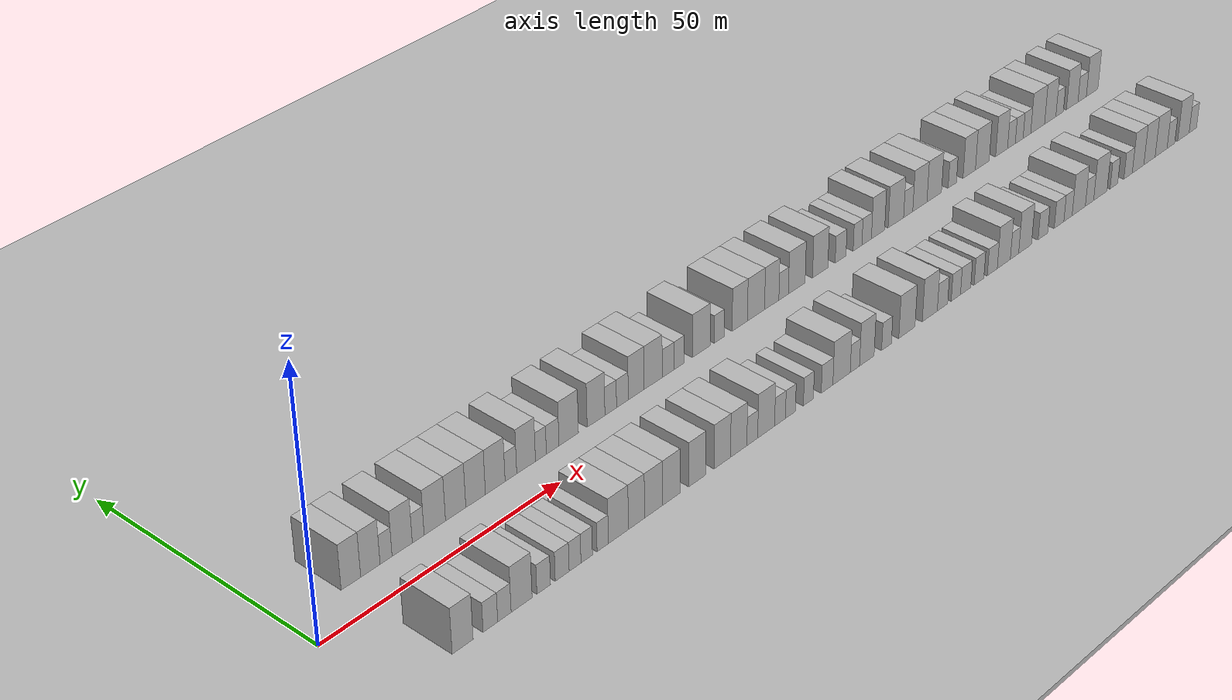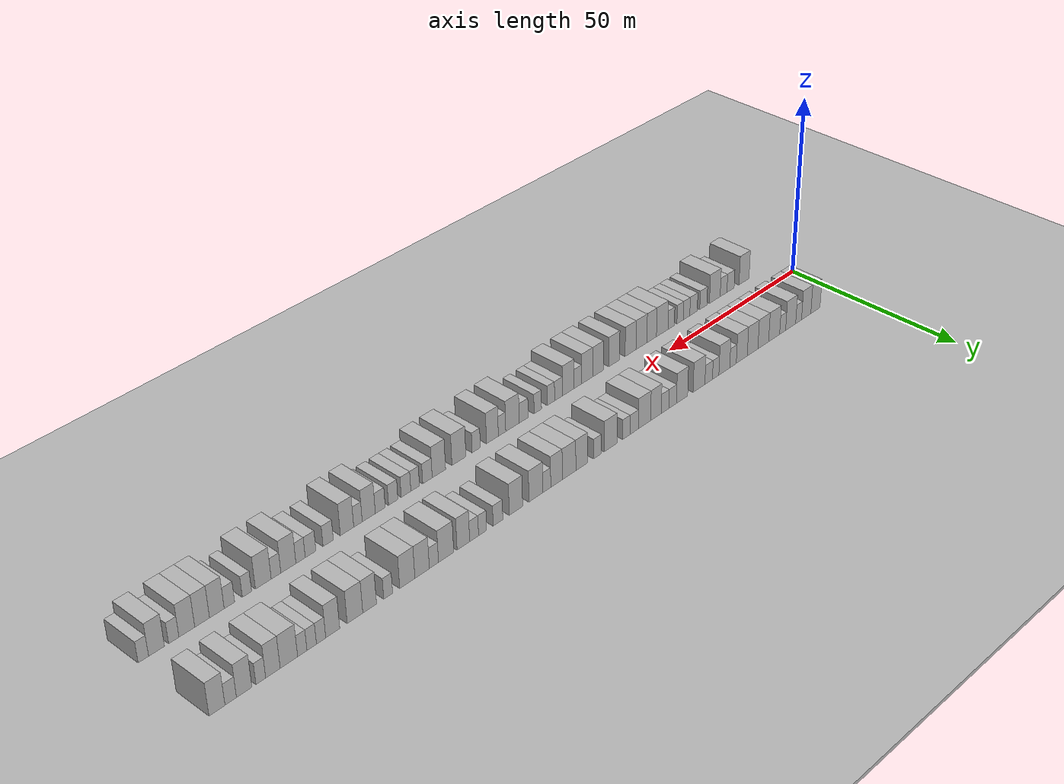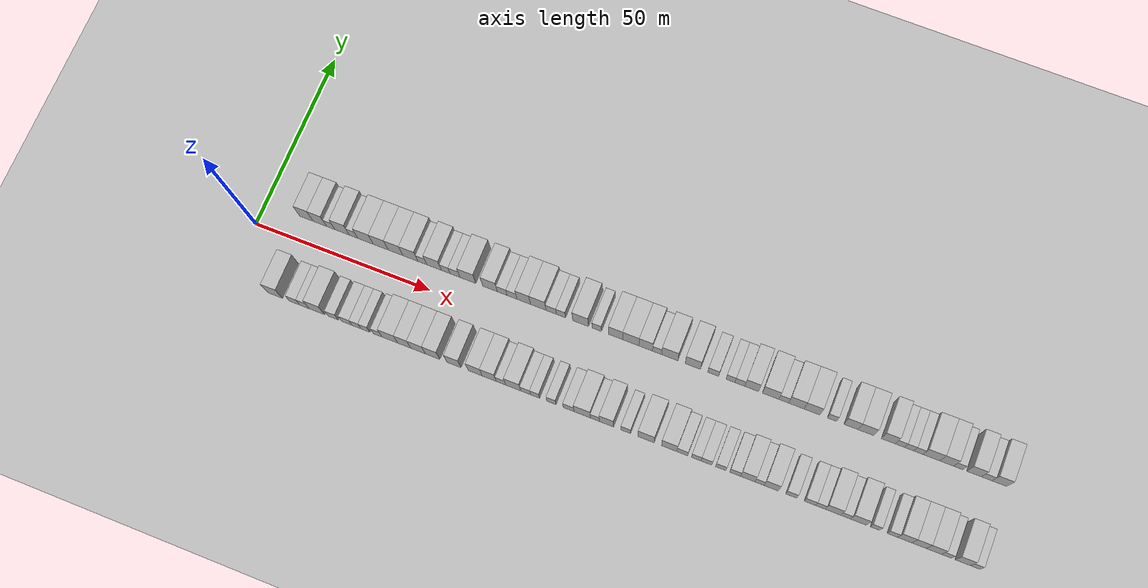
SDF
<?xml version="1.0" encoding="utf-8"?>

<sdf version="1.6">

   <world name="default">

      <gui fullscreen="0">

         <camera name="user_camera">

            <pose>-15 0 4.57585 0 0 0</pose>

            <view_controller>orbit</view_controller>

         </camera>

      </gui>

      <scene>

         <sky>

           <clouds>

             <speed>12</speed>

           </clouds>

         </sky>

         <ambient>0.4 0.4 0.4 1</ambient>

         <background>0.7 0.7 0.7 1</background>

         <shadows>1</shadows>

      </scene>

      <gravity>0 0 -9.8066</gravity>

      <magnetic_field>6e-06 2.3e-05 -4.2e-05</magnetic_field>

      <physics default="0" name="default_physics" type="ode">

         <ode>

            <solver>

               <type>quick</type>

               <iters>10</iters>

               <sor>1.0</sor>

               <use_dynamic_moi_rescaling>0</use_dynamic_moi_rescaling>

            </solver>

            <constraints>

               <cfm>0</cfm>

               <erp>0.2</erp>

               <contact_max_correcting_vel>100</contact_max_correcting_vel>

               <contact_surface_layer>0.001</contact_surface_layer>

            </constraints>

         </ode>

         <max_step_size>0.004</max_step_size>

         <real_time_factor>1</real_time_factor>

         <real_time_update_rate>250</real_time_update_rate>

      </physics>

      <light name="sun" type="directional">

         <cast_shadows>1</cast_shadows>

         <pose>0 0 10 0 0 0</pose>

         <diffuse>0.8 0.8 0.8 1</diffuse>

         <specular>0.2 0.2 0.2 1</specular>

         <attenuation>

            <range>1000</range>

            <constant>0.9</constant>

            <linear>0.01</linear>

            <quadratic>0.001</quadratic>

         </attenuation>

         <direction>-0.5 0.1 -0.9</direction>

      </light>

      <include>

         <name>ground_plane_1</name>

         <uri>model://HANNAS_ground_plane</uri>

         <pose>0 0 0  0 0 0</pose>

      </include>

      <include>

         <name>ground_plane_2</name>

         <uri>model://HANNAS_ground_plane</uri>

         <pose>100 0 0  0 0 0</pose>

      </include>

      <model name="building_1">

         <static>1</static>

         <pose frame="">11.9366 11.0000 0 0.000000 0.000000 1.570796</pose>

         <link name="link">

            <pose frame="">0 0 4.50 0 0 0</pose>

            <collision name="collision">

               <geometry>

                  <box>

                     <size>10.0000 3.8731 9.0000</size>

                  </box>

               </geometry>

               <max_contacts>10</max_contacts>

               <surface>

                  <contact>

                     <ode/>

                  </contact>

                  <bounce/>

                  <friction>

                     <torsional>

                        <ode/>

                     </torsional>

                     <ode/>

                  </friction>

               </surface>

            </collision>

            <visual name="visual">

               <cast_shadows>0</cast_shadows>

               <geometry>

                  <box>

                     <size>10.0000 3.8731 9.0000</size>

                  </box>

               </geometry>

               <material>

                  <script>

                     <uri>model://HANNAS_wall/materials/scripts</uri>

                     <uri>model://HANNAS_wall/materials/textures</uri>

                     <name>vrc/HANNAS_wall</name>

                  </script>

               </material>

            </visual>

            <self_collide>0</self_collide>

            <enable_wind>0</enable_wind>

            <kinematic>0</kinematic>

         </link>

      </model>

      <model name="building_2">

         <static>1</static>

         <pose frame="">15.8093 11.0000 0 0.000000 0.000000 1.570796</pose>

         <link name="link">

            <pose frame="">0 0 4.50 0 0 0</pose>

            <collision name="collision">

               <geometry>

                  <box>

                     <size>10.0000 3.8724 9.0000</size>

                  </box>

               </geometry>

               <max_contacts>10</max_contacts>

               <surface>

                  <contact>

                     <ode/>

                  </contact>

                  <bounce/>

                  <friction>

                     <torsional>

                        <ode/>

                     </torsional>

                     <ode/>

                  </friction>

               </surface>

            </collision>

            <visual name="visual">

               <cast_shadows>0</cast_shadows>

               <geometry>

                  <box>

                     <size>10.0000 3.8724 9.0000</size>

                  </box>

               </geometry>

               <material>

                  <script>

                     <uri>model://HANNAS_wall/materials/scripts</uri>

                     <uri>model://HANNAS_wall/materials/textures</uri>

                     <name>vrc/HANNAS_wall</name>

                  </script>

               </material>

            </visual>

            <self_collide>0</self_collide>

            <enable_wind>0</enable_wind>

            <kinematic>0</kinematic>

         </link>

      </model>

      <model name="building_3">

         <static>1</static>

         <pose frame="">18.9615 11.0000 0 0.000000 0.000000 1.570796</pose>

         <link name="link">

            <pose frame="">0 0 3.00 0 0 0</pose>

            <collision name="collision">

               <geometry>

                  <box>

                     <size>10.0000 2.4319 6.0000</size>

                  </box>

               </geometry>

               <max_contacts>10</max_contacts>

               <surface>

                  <contact>

                     <ode/>

                  </contact>

                  <bounce/>

                  <friction>

                     <torsional>

                        <ode/>

                     </torsional>

                     <ode/>

                  </friction>

               </surface>

            </collision>

            <visual name="visual">

               <cast_shadows>0</cast_shadows>

               <geometry>

                  <box>

                     <size>10.0000 2.4319 6.0000</size>

                  </box>

               </geometry>

               <material>

                  <script>

                     <uri>model://HANNAS_wall/materials/scripts</uri>

                     <uri>model://HANNAS_wall/materials/textures</uri>

                     <name>vrc/HANNAS_wall</name>

                  </script>

               </material>

            </visual>

            <self_collide>0</self_collide>

            <enable_wind>0</enable_wind>

            <kinematic>0</kinematic>

         </link>

      </model>

      <model name="building_4">

         <static>1</static>

         <pose frame="">22.2412 11.0000 0 0.000000 0.000000 1.570796</pose>

         <link name="link">

            <pose frame="">0 0 4.50 0 0 0</pose>

            <collision name="collision">

               <geometry>

                  <box>

                     <size>10.0000 4.1276 9.0000</size>

                  </box>

               </geometry>

               <max_contacts>10</max_contacts>

               <surface>

                  <contact>

                     <ode/>

                  </contact>

                  <bounce/>

                  <friction>

                     <torsional>

                        <ode/>

                     </torsional>

                     <ode/>

                  </friction>

               </surface>

            </collision>

            <visual name="visual">

               <cast_shadows>0</cast_shadows>

               <geometry>

                  <box>

                     <size>10.0000 4.1276 9.0000</size>

                  </box>

               </geometry>

               <material>

                  <script>

                     <uri>model://HANNAS_wall/materials/scripts</uri>

                     <uri>model://HANNAS_wall/materials/textures</uri>

                     <name>vrc/HANNAS_wall</name>

                  </script>

               </material>

            </visual>

            <self_collide>0</self_collide>

            <enable_wind>0</enable_wind>

            <kinematic>0</kinematic>

         </link>

      </model>

      <model name="building_5">

         <static>1</static>

         <pose frame="">25.5283 11.0000 0 0.000000 0.000000 1.570796</pose>

         <link name="link">

            <pose frame="">0 0 3.00 0 0 0</pose>

            <collision name="collision">

               <geometry>

                  <box>

                     <size>10.0000 2.4465 6.0000</size>

                  </box>

               </geometry>

               <max_contacts>10</max_contacts>

               <surface>

                  <contact>

                     <ode/>

                  </contact>

                  <bounce/>

                  <friction>

                     <torsional>

                        <ode/>

                     </torsional>

                     <ode/>

                  </friction>

               </surface>

            </collision>

            <visual name="visual">

               <cast_shadows>0</cast_shadows>

               <geometry>

                  <box>

                     <size>10.0000 2.4465 6.0000</size>

                  </box>

               </geometry>

               <material>

                  <script>

                     <uri>model://HANNAS_wall/materials/scripts</uri>

                     <uri>model://HANNAS_wall/materials/textures</uri>

                     <name>vrc/HANNAS_wall</name>

                  </script>

               </material>

            </visual>

            <self_collide>0</self_collide>

            <enable_wind>0</enable_wind>

            <kinematic>0</kinematic>

         </link>

      </model>

      <model name="building_6">

         <static>1</static>

         <pose frame="">28.9808 11.0000 0 0.000000 0.000000 1.570796</pose>

         <link name="link">

            <pose frame="">0 0 4.50 0 0 0</pose>

            <collision name="collision">

               <geometry>

                  <box>

                     <size>10.0000 4.4585 9.0000</size>

                  </box>

               </geometry>

               <max_contacts>10</max_contacts>

               <surface>

                  <contact>

                     <ode/>

                  </contact>

                  <bounce/>

                  <friction>

                     <torsional>

                        <ode/>

                     </torsional>

                     <ode/>

                  </friction>

               </surface>

            </collision>

            <visual name="visual">

               <cast_shadows>0</cast_shadows>

               <geometry>

                  <box>

                     <size>10.0000 4.4585 9.0000</size>

                  </box>

               </geometry>

               <material>

                  <script>

                     <uri>model://HANNAS_wall/materials/scripts</uri>

                     <uri>model://HANNAS_wall/materials/textures</uri>

                     <name>vrc/HANNAS_wall</name>

                  </script>

               </material>

            </visual>

            <self_collide>0</self_collide>

            <enable_wind>0</enable_wind>

            <kinematic>0</kinematic>

         </link>

      </model>

      <model name="building_7">

         <static>1</static>

         <pose frame="">33.3568 11.0000 0 0.000000 0.000000 1.570796</pose>

         <link name="link">

            <pose frame="">0 0 4.50 0 0 0</pose>

            <collision name="collision">

               <geometry>

                  <box>

                     <size>10.0000 4.2935 9.0000</size>

                  </box>

               </geometry>

               <max_contacts>10</max_contacts>

               <surface>

                  <contact>

                     <ode/>

                  </contact>

                  <bounce/>

                  <friction>

                     <torsional>

                        <ode/>

                     </torsional>

                     <ode/>

                  </friction>

               </surface>

            </collision>

            <visual name="visual">

               <cast_shadows>0</cast_shadows>

               <geometry>

                  <box>

                     <size>10.0000 4.2935 9.0000</size>

                  </box>

               </geometry>

               <material>

                  <script>

                     <uri>model://HANNAS_wall/materials/scripts</uri>

                     <uri>model://HANNAS_wall/materials/textures</uri>

                     <name>vrc/HANNAS_wall</name>

                  </script>

               </material>

            </visual>

            <self_collide>0</self_collide>

            <enable_wind>0</enable_wind>

            <kinematic>0</kinematic>

         </link>

      </model>

      <model name="building_8">

         <static>1</static>

         <pose frame="">37.6068 11.0000 0 0.000000 0.000000 1.570796</pose>

         <link name="link">

            <pose frame="">0 0 4.50 0 0 0</pose>

            <collision name="collision">

               <geometry>

                  <box>

                     <size>10.0000 4.2064 9.0000</size>

                  </box>

               </geometry>

               <max_contacts>10</max_contacts>

               <surface>

                  <contact>

                     <ode/>

                  </contact>

                  <bounce/>

                  <friction>

                     <torsional>

                        <ode/>

                     </torsional>

                     <ode/>

                  </friction>

               </surface>

            </collision>

            <visual name="visual">

               <cast_shadows>0</cast_shadows>

               <geometry>

                  <box>

                     <size>10.0000 4.2064 9.0000</size>

                  </box>

               </geometry>

               <material>

                  <script>

                     <uri>model://HANNAS_wall/materials/scripts</uri>

                     <uri>model://HANNAS_wall/materials/textures</uri>

                     <name>vrc/HANNAS_wall</name>

                  </script>

               </material>

            </visual>

            <self_collide>0</self_collide>

            <enable_wind>0</enable_wind>

            <kinematic>0</kinematic>

         </link>

      </model>

      <model name="building_9">

         <static>1</static>

         <pose frame="">41.8423 11.0000 0 0.000000 0.000000 1.570796</pose>

         <link name="link">

            <pose frame="">0 0 4.50 0 0 0</pose>

            <collision name="collision">

               <geometry>

                  <box>

                     <size>10.0000 4.2647 9.0000</size>

                  </box>

               </geometry>

               <max_contacts>10</max_contacts>

               <surface>

                  <contact>

                     <ode/>

                  </contact>

                  <bounce/>

                  <friction>

                     <torsional>

                        <ode/>

                     </torsional>

                     <ode/>

                  </friction>

               </surface>

            </collision>

            <visual name="visual">

               <cast_shadows>0</cast_shadows>

               <geometry>

                  <box>

                     <size>10.0000 4.2647 9.0000</size>

                  </box>

               </geometry>

               <material>

                  <script>

                     <uri>model://HANNAS_wall/materials/scripts</uri>

                     <uri>model://HANNAS_wall/materials/textures</uri>

                     <name>vrc/HANNAS_wall</name>

                  </script>

               </material>

            </visual>

            <self_collide>0</self_collide>

            <enable_wind>0</enable_wind>

            <kinematic>0</kinematic>

         </link>

      </model>

      <model name="building_10">

         <static>1</static>

         <pose frame="">45.2509 11.0000 0 0.000000 0.000000 1.570796</pose>

         <link name="link">

            <pose frame="">0 0 3.00 0 0 0</pose>

            <collision name="collision">

               <geometry>

                  <box>

                     <size>10.0000 2.5525 6.0000</size>

                  </box>

               </geometry>

               <max_contacts>10</max_contacts>

               <surface>

                  <contact>

                     <ode/>

                  </contact>

                  <bounce/>

                  <friction>

                     <torsional>

                        <ode/>

                     </torsional>

                     <ode/>

                  </friction>

               </surface>

            </collision>

            <visual name="visual">

               <cast_shadows>0</cast_shadows>

               <geometry>

                  <box>

                     <size>10.0000 2.5525 6.0000</size>

                  </box>

               </geometry>

               <material>

                  <script>

                     <uri>model://HANNAS_wall/materials/scripts</uri>

                     <uri>model://HANNAS_wall/materials/textures</uri>

                     <name>vrc/HANNAS_wall</name>

                  </script>

               </material>

            </visual>

            <self_collide>0</self_collide>

            <enable_wind>0</enable_wind>

            <kinematic>0</kinematic>

         </link>

      </model>

      <model name="building_11">

         <static>1</static>

         <pose frame="">48.6036 11.0000 0 0.000000 0.000000 1.570796</pose>

         <link name="link">

            <pose frame="">0 0 4.50 0 0 0</pose>

            <collision name="collision">

               <geometry>

                  <box>

                     <size>10.0000 4.1528 9.0000</size>

                  </box>

               </geometry>

               <max_contacts>10</max_contacts>

               <surface>

                  <contact>

                     <ode/>

                  </contact>

                  <bounce/>

                  <friction>

                     <torsional>

                        <ode/>

                     </torsional>

                     <ode/>

                  </friction>

               </surface>

            </collision>

            <visual name="visual">

               <cast_shadows>0</cast_shadows>

               <geometry>

                  <box>

                     <size>10.0000 4.1528 9.0000</size>

                  </box>

               </geometry>

               <material>

                  <script>

                     <uri>model://HANNAS_wall/materials/scripts</uri>

                     <uri>model://HANNAS_wall/materials/textures</uri>

                     <name>vrc/HANNAS_wall</name>

                  </script>

               </material>

            </visual>

            <self_collide>0</self_collide>

            <enable_wind>0</enable_wind>

            <kinematic>0</kinematic>

         </link>

      </model>

      <model name="building_12">

         <static>1</static>

         <pose frame="">51.9011 11.0000 0 0.000000 0.000000 1.570796</pose>

         <link name="link">

            <pose frame="">0 0 3.00 0 0 0</pose>

            <collision name="collision">

               <geometry>

                  <box>

                     <size>10.0000 2.4423 6.0000</size>

                  </box>

               </geometry>

               <max_contacts>10</max_contacts>

               <surface>

                  <contact>

                     <ode/>

                  </contact>

                  <bounce/>

                  <friction>

                     <torsional>

                        <ode/>

                     </torsional>

                     <ode/>

                  </friction>

               </surface>

            </collision>

            <visual name="visual">

               <cast_shadows>0</cast_shadows>

               <geometry>

                  <box>

                     <size>10.0000 2.4423 6.0000</size>

                  </box>

               </geometry>

               <material>

                  <script>

                     <uri>model://HANNAS_wall/materials/scripts</uri>

                     <uri>model://HANNAS_wall/materials/textures</uri>

                     <name>vrc/HANNAS_wall</name>

                  </script>

               </material>

            </visual>

            <self_collide>0</self_collide>

            <enable_wind>0</enable_wind>

            <kinematic>0</kinematic>

         </link>

      </model>

      <model name="building_13">

         <static>1</static>

         <pose frame="">54.5475 11.0000 0 0.000000 0.000000 1.570796</pose>

         <link name="link">

            <pose frame="">0 0 3.00 0 0 0</pose>

            <collision name="collision">

               <geometry>

                  <box>

                     <size>10.0000 2.8504 6.0000</size>

                  </box>

               </geometry>

               <max_contacts>10</max_contacts>

               <surface>

                  <contact>

                     <ode/>

                  </contact>

                  <bounce/>

                  <friction>

                     <torsional>

                        <ode/>

                     </torsional>

                     <ode/>

                  </friction>

               </surface>

            </collision>

            <visual name="visual">

               <cast_shadows>0</cast_shadows>

               <geometry>

                  <box>

                     <size>10.0000 2.8504 6.0000</size>

                  </box>

               </geometry>

               <material>

                  <script>

                     <uri>model://HANNAS_wall/materials/scripts</uri>

                     <uri>model://HANNAS_wall/materials/textures</uri>

                     <name>vrc/HANNAS_wall</name>

                  </script>

               </material>

            </visual>

            <self_collide>0</self_collide>

            <enable_wind>0</enable_wind>

            <kinematic>0</kinematic>

         </link>

      </model>

      <model name="building_14">

         <static>1</static>

         <pose frame="">58.1866 11.0000 0 0.000000 0.000000 1.570796</pose>

         <link name="link">

            <pose frame="">0 0 4.50 0 0 0</pose>

            <collision name="collision">

               <geometry>

                  <box>

                     <size>10.0000 4.4278 9.0000</size>

                  </box>

               </geometry>

               <max_contacts>10</max_contacts>

               <surface>

                  <contact>

                     <ode/>

                  </contact>

                  <bounce/>

                  <friction>

                     <torsional>

                        <ode/>

                     </torsional>

                     <ode/>

                  </friction>

               </surface>

            </collision>

            <visual name="visual">

               <cast_shadows>0</cast_shadows>

               <geometry>

                  <box>

                     <size>10.0000 4.4278 9.0000</size>

                  </box>

               </geometry>

               <material>

                  <script>

                     <uri>model://HANNAS_wall/materials/scripts</uri>

                     <uri>model://HANNAS_wall/materials/textures</uri>

                     <name>vrc/HANNAS_wall</name>

                  </script>

               </material>

            </visual>

            <self_collide>0</self_collide>

            <enable_wind>0</enable_wind>

            <kinematic>0</kinematic>

         </link>

      </model>

      <model name="building_15">

         <static>1</static>

         <pose frame="">64.4646 11.0000 0 0.000000 0.000000 1.570796</pose>

         <link name="link">

            <pose frame="">0 0 4.50 0 0 0</pose>

            <collision name="collision">

               <geometry>

                  <box>

                     <size>10.0000 4.1282 9.0000</size>

                  </box>

               </geometry>

               <max_contacts>10</max_contacts>

               <surface>

                  <contact>

                     <ode/>

                  </contact>

                  <bounce/>

                  <friction>

                     <torsional>

                        <ode/>

                     </torsional>

                     <ode/>

                  </friction>

               </surface>

            </collision>

            <visual name="visual">

               <cast_shadows>0</cast_shadows>

               <geometry>

                  <box>

                     <size>10.0000 4.1282 9.0000</size>

                  </box>

               </geometry>

               <material>

                  <script>

                     <uri>model://HANNAS_wall/materials/scripts</uri>

                     <uri>model://HANNAS_wall/materials/textures</uri>

                     <name>vrc/HANNAS_wall</name>

                  </script>

               </material>

            </visual>

            <self_collide>0</self_collide>

            <enable_wind>0</enable_wind>

            <kinematic>0</kinematic>

         </link>

      </model>

      <model name="building_16">

         <static>1</static>

         <pose frame="">67.8935 11.0000 0 0.000000 0.000000 1.570796</pose>

         <link name="link">

            <pose frame="">0 0 3.00 0 0 0</pose>

            <collision name="collision">

               <geometry>

                  <box>

                     <size>10.0000 2.7296 6.0000</size>

                  </box>

               </geometry>

               <max_contacts>10</max_contacts>

               <surface>

                  <contact>

                     <ode/>

                  </contact>

                  <bounce/>

                  <friction>

                     <torsional>

                        <ode/>

                     </torsional>

                     <ode/>

                  </friction>

               </surface>

            </collision>

            <visual name="visual">

               <cast_shadows>0</cast_shadows>

               <geometry>

                  <box>

                     <size>10.0000 2.7296 6.0000</size>

                  </box>

               </geometry>

               <material>

                  <script>

                     <uri>model://HANNAS_wall/materials/scripts</uri>

                     <uri>model://HANNAS_wall/materials/textures</uri>

                     <name>vrc/HANNAS_wall</name>

                  </script>

               </material>

            </visual>

            <self_collide>0</self_collide>

            <enable_wind>0</enable_wind>

            <kinematic>0</kinematic>

         </link>

      </model>

      <model name="building_17">

         <static>1</static>

         <pose frame="">70.6491 11.0000 0 0.000000 0.000000 1.570796</pose>

         <link name="link">

            <pose frame="">0 0 3.00 0 0 0</pose>

            <collision name="collision">

               <geometry>

                  <box>

                     <size>10.0000 2.7816 6.0000</size>

                  </box>

               </geometry>

               <max_contacts>10</max_contacts>

               <surface>

                  <contact>

                     <ode/>

                  </contact>

                  <bounce/>

                  <friction>

                     <torsional>

                        <ode/>

                     </torsional>

                     <ode/>

                  </friction>

               </surface>

            </collision>

            <visual name="visual">

               <cast_shadows>0</cast_shadows>

               <geometry>

                  <box>

                     <size>10.0000 2.7816 6.0000</size>

                  </box>

               </geometry>

               <material>

                  <script>

                     <uri>model://HANNAS_wall/materials/scripts</uri>

                     <uri>model://HANNAS_wall/materials/textures</uri>

                     <name>vrc/HANNAS_wall</name>

                  </script>

               </material>

            </visual>

            <self_collide>0</self_collide>

            <enable_wind>0</enable_wind>

            <kinematic>0</kinematic>

         </link>

      </model>

      <model name="building_18">

         <static>1</static>

         <pose frame="">73.9400 11.0000 0 0.000000 0.000000 1.570796</pose>

         <link name="link">

            <pose frame="">0 0 4.50 0 0 0</pose>

            <collision name="collision">

               <geometry>

                  <box>

                     <size>10.0000 3.8002 9.0000</size>

                  </box>

               </geometry>

               <max_contacts>10</max_contacts>

               <surface>

                  <contact>

                     <ode/>

                  </contact>

                  <bounce/>

                  <friction>

                     <torsional>

                        <ode/>

                     </torsional>

                     <ode/>

                  </friction>

               </surface>

            </collision>

            <visual name="visual">

               <cast_shadows>0</cast_shadows>

               <geometry>

                  <box>

                     <size>10.0000 3.8002 9.0000</size>

                  </box>

               </geometry>

               <material>

                  <script>

                     <uri>model://HANNAS_wall/materials/scripts</uri>

                     <uri>model://HANNAS_wall/materials/textures</uri>

                     <name>vrc/HANNAS_wall</name>

                  </script>

               </material>

            </visual>

            <self_collide>0</self_collide>

            <enable_wind>0</enable_wind>

            <kinematic>0</kinematic>

         </link>

      </model>

      <model name="building_19">

         <static>1</static>

         <pose frame="">78.0126 11.0000 0 0.000000 0.000000 1.570796</pose>

         <link name="link">

            <pose frame="">0 0 4.50 0 0 0</pose>

            <collision name="collision">

               <geometry>

                  <box>

                     <size>10.0000 4.3451 9.0000</size>

                  </box>

               </geometry>

               <max_contacts>10</max_contacts>

               <surface>

                  <contact>

                     <ode/>

                  </contact>

                  <bounce/>

                  <friction>

                     <torsional>

                        <ode/>

                     </torsional>

                     <ode/>

                  </friction>

               </surface>

            </collision>

            <visual name="visual">

               <cast_shadows>0</cast_shadows>

               <geometry>

                  <box>

                     <size>10.0000 4.3451 9.0000</size>

                  </box>

               </geometry>

               <material>

                  <script>

                     <uri>model://HANNAS_wall/materials/scripts</uri>

                     <uri>model://HANNAS_wall/materials/textures</uri>

                     <name>vrc/HANNAS_wall</name>

                  </script>

               </material>

            </visual>

            <self_collide>0</self_collide>

            <enable_wind>0</enable_wind>

            <kinematic>0</kinematic>

         </link>

      </model>

      <model name="building_20">

         <static>1</static>

         <pose frame="">81.6403 11.0000 0 0.000000 0.000000 1.570796</pose>

         <link name="link">

            <pose frame="">0 0 3.00 0 0 0</pose>

            <collision name="collision">

               <geometry>

                  <box>

                     <size>10.0000 2.9102 6.0000</size>

                  </box>

               </geometry>

               <max_contacts>10</max_contacts>

               <surface>

                  <contact>

                     <ode/>

                  </contact>

                  <bounce/>

                  <friction>

                     <torsional>

                        <ode/>

                     </torsional>

                     <ode/>

                  </friction>

               </surface>

            </collision>

            <visual name="visual">

               <cast_shadows>0</cast_shadows>

               <geometry>

                  <box>

                     <size>10.0000 2.9102 6.0000</size>

                  </box>

               </geometry>

               <material>

                  <script>

                     <uri>model://HANNAS_wall/materials/scripts</uri>

                     <uri>model://HANNAS_wall/materials/textures</uri>

                     <name>vrc/HANNAS_wall</name>

                  </script>

               </material>

            </visual>

            <self_collide>0</self_collide>

            <enable_wind>0</enable_wind>

            <kinematic>0</kinematic>

         </link>

      </model>

      <model name="building_21">

         <static>1</static>

         <pose frame="">84.3688 11.0000 0 0.000000 0.000000 1.570796</pose>

         <link name="link">

            <pose frame="">0 0 3.00 0 0 0</pose>

            <collision name="collision">

               <geometry>

                  <box>

                     <size>10.0000 2.5467 6.0000</size>

                  </box>

               </geometry>

               <max_contacts>10</max_contacts>

               <surface>

                  <contact>

                     <ode/>

                  </contact>

                  <bounce/>

                  <friction>

                     <torsional>

                        <ode/>

                     </torsional>

                     <ode/>

                  </friction>

               </surface>

            </collision>

            <visual name="visual">

               <cast_shadows>0</cast_shadows>

               <geometry>

                  <box>

                     <size>10.0000 2.5467 6.0000</size>

                  </box>

               </geometry>

               <material>

                  <script>

                     <uri>model://HANNAS_wall/materials/scripts</uri>

                     <uri>model://HANNAS_wall/materials/textures</uri>

                     <name>vrc/HANNAS_wall</name>

                  </script>

               </material>

            </visual>

            <self_collide>0</self_collide>

            <enable_wind>0</enable_wind>

            <kinematic>0</kinematic>

         </link>

      </model>

      <model name="building_22">

         <static>1</static>

         <pose frame="">89.8376 11.0000 0 0.000000 0.000000 1.570796</pose>

         <link name="link">

            <pose frame="">0 0 4.50 0 0 0</pose>

            <collision name="collision">

               <geometry>

                  <box>

                     <size>10.0000 4.3909 9.0000</size>

                  </box>

               </geometry>

               <max_contacts>10</max_contacts>

               <surface>

                  <contact>

                     <ode/>

                  </contact>

                  <bounce/>

                  <friction>

                     <torsional>

                        <ode/>

                     </torsional>

                     <ode/>

                  </friction>

               </surface>

            </collision>

            <visual name="visual">

               <cast_shadows>0</cast_shadows>

               <geometry>

                  <box>

                     <size>10.0000 4.3909 9.0000</size>

                  </box>

               </geometry>

               <material>

                  <script>

                     <uri>model://HANNAS_wall/materials/scripts</uri>

                     <uri>model://HANNAS_wall/materials/textures</uri>

                     <name>vrc/HANNAS_wall</name>

                  </script>

               </material>

            </visual>

            <self_collide>0</self_collide>

            <enable_wind>0</enable_wind>

            <kinematic>0</kinematic>

         </link>

      </model>

      <model name="building_23">

         <static>1</static>

         <pose frame="">94.3251 11.0000 0 0.000000 0.000000 1.570796</pose>

         <link name="link">

            <pose frame="">0 0 3.00 0 0 0</pose>

            <collision name="collision">

               <geometry>

                  <box>

                     <size>10.0000 2.5842 6.0000</size>

                  </box>

               </geometry>

               <max_contacts>10</max_contacts>

               <surface>

                  <contact>

                     <ode/>

                  </contact>

                  <bounce/>

                  <friction>

                     <torsional>

                        <ode/>

                     </torsional>

                     <ode/>

                  </friction>

               </surface>

            </collision>

            <visual name="visual">

               <cast_shadows>0</cast_shadows>

               <geometry>

                  <box>

                     <size>10.0000 2.5842 6.0000</size>

                  </box>

               </geometry>

               <material>

                  <script>

                     <uri>model://HANNAS_wall/materials/scripts</uri>

                     <uri>model://HANNAS_wall/materials/textures</uri>

                     <name>vrc/HANNAS_wall</name>

                  </script>

               </material>

            </visual>

            <self_collide>0</self_collide>

            <enable_wind>0</enable_wind>

            <kinematic>0</kinematic>

         </link>

      </model>

      <model name="building_24">

         <static>1</static>

         <pose frame="">99.5820 11.0000 0 0.000000 0.000000 1.570796</pose>

         <link name="link">

            <pose frame="">0 0 4.50 0 0 0</pose>

            <collision name="collision">

               <geometry>

                  <box>

                     <size>10.0000 3.9297 9.0000</size>

                  </box>

               </geometry>

               <max_contacts>10</max_contacts>

               <surface>

                  <contact>

                     <ode/>

                  </contact>

                  <bounce/>

                  <friction>

                     <torsional>

                        <ode/>

                     </torsional>

                     <ode/>

                  </friction>

               </surface>

            </collision>

            <visual name="visual">

               <cast_shadows>0</cast_shadows>

               <geometry>

                  <box>

                     <size>10.0000 3.9297 9.0000</size>

                  </box>

               </geometry>

               <material>

                  <script>

                     <uri>model://HANNAS_wall/materials/scripts</uri>

                     <uri>model://HANNAS_wall/materials/textures</uri>

                     <name>vrc/HANNAS_wall</name>

                  </script>

               </material>

            </visual>

            <self_collide>0</self_collide>

            <enable_wind>0</enable_wind>

            <kinematic>0</kinematic>

         </link>

      </model>

      <model name="building_25">

         <static>1</static>

         <pose frame="">103.7724 11.0000 0 0.000000 0.000000 1.570796</pose>

         <link name="link">

            <pose frame="">0 0 4.50 0 0 0</pose>

            <collision name="collision">

               <geometry>

                  <box>

                     <size>10.0000 4.4511 9.0000</size>

                  </box>

               </geometry>

               <max_contacts>10</max_contacts>

               <surface>

                  <contact>

                     <ode/>

                  </contact>

                  <bounce/>

                  <friction>

                     <torsional>

                        <ode/>

                     </torsional>

                     <ode/>

                  </friction>

               </surface>

            </collision>

            <visual name="visual">

               <cast_shadows>0</cast_shadows>

               <geometry>

                  <box>

                     <size>10.0000 4.4511 9.0000</size>

                  </box>

               </geometry>

               <material>

                  <script>

                     <uri>model://HANNAS_wall/materials/scripts</uri>

                     <uri>model://HANNAS_wall/materials/textures</uri>

                     <name>vrc/HANNAS_wall</name>

                  </script>

               </material>

            </visual>

            <self_collide>0</self_collide>

            <enable_wind>0</enable_wind>

            <kinematic>0</kinematic>

         </link>

      </model>

      <model name="building_26">

         <static>1</static>

         <pose frame="">107.8784 11.0000 0 0.000000 0.000000 1.570796</pose>

         <link name="link">

            <pose frame="">0 0 4.50 0 0 0</pose>

            <collision name="collision">

               <geometry>

                  <box>

                     <size>10.0000 3.7609 9.0000</size>

                  </box>

               </geometry>

               <max_contacts>10</max_contacts>

               <surface>

                  <contact>

                     <ode/>

                  </contact>

                  <bounce/>

                  <friction>

                     <torsional>

                        <ode/>

                     </torsional>

                     <ode/>

                  </friction>

               </surface>

            </collision>

            <visual name="visual">

               <cast_shadows>0</cast_shadows>

               <geometry>

                  <box>

                     <size>10.0000 3.7609 9.0000</size>

                  </box>

               </geometry>

               <material>

                  <script>

                     <uri>model://HANNAS_wall/materials/scripts</uri>

                     <uri>model://HANNAS_wall/materials/textures</uri>

                     <name>vrc/HANNAS_wall</name>

                  </script>

               </material>

            </visual>

            <self_collide>0</self_collide>

            <enable_wind>0</enable_wind>

            <kinematic>0</kinematic>

         </link>

      </model>

      <model name="building_27">

         <static>1</static>

         <pose frame="">111.0178 11.0000 0 0.000000 0.000000 1.570796</pose>

         <link name="link">

            <pose frame="">0 0 3.00 0 0 0</pose>

            <collision name="collision">

               <geometry>

                  <box>

                     <size>10.0000 2.5179 6.0000</size>

                  </box>

               </geometry>

               <max_contacts>10</max_contacts>

               <surface>

                  <contact>

                     <ode/>

                  </contact>

                  <bounce/>

                  <friction>

                     <torsional>

                        <ode/>

                     </torsional>

                     <ode/>

                  </friction>

               </surface>

            </collision>

            <visual name="visual">

               <cast_shadows>0</cast_shadows>

               <geometry>

                  <box>

                     <size>10.0000 2.5179 6.0000</size>

                  </box>

               </geometry>

               <material>

                  <script>

                     <uri>model://HANNAS_wall/materials/scripts</uri>

                     <uri>model://HANNAS_wall/materials/textures</uri>

                     <name>vrc/HANNAS_wall</name>

                  </script>

               </material>

            </visual>

            <self_collide>0</self_collide>

            <enable_wind>0</enable_wind>

            <kinematic>0</kinematic>

         </link>

      </model>

      <model name="building_28">

         <static>1</static>

         <pose frame="">114.5149 11.0000 0 0.000000 0.000000 1.570796</pose>

         <link name="link">

            <pose frame="">0 0 4.50 0 0 0</pose>

            <collision name="collision">

               <geometry>

                  <box>

                     <size>10.0000 4.4763 9.0000</size>

                  </box>

               </geometry>

               <max_contacts>10</max_contacts>

               <surface>

                  <contact>

                     <ode/>

                  </contact>

                  <bounce/>

                  <friction>

                     <torsional>

                        <ode/>

                     </torsional>

                     <ode/>

                  </friction>

               </surface>

            </collision>

            <visual name="visual">

               <cast_shadows>0</cast_shadows>

               <geometry>

                  <box>

                     <size>10.0000 4.4763 9.0000</size>

                  </box>

               </geometry>

               <material>

                  <script>

                     <uri>model://HANNAS_wall/materials/scripts</uri>

                     <uri>model://HANNAS_wall/materials/textures</uri>

                     <name>vrc/HANNAS_wall</name>

                  </script>

               </material>

            </visual>

            <self_collide>0</self_collide>

            <enable_wind>0</enable_wind>

            <kinematic>0</kinematic>

         </link>

      </model>

      <model name="building_29">

         <static>1</static>

         <pose frame="">120.8508 11.0000 0 0.000000 0.000000 1.570796</pose>

         <link name="link">

            <pose frame="">0 0 4.50 0 0 0</pose>

            <collision name="collision">

               <geometry>

                  <box>

                     <size>10.0000 4.1954 9.0000</size>

                  </box>

               </geometry>

               <max_contacts>10</max_contacts>

               <surface>

                  <contact>

                     <ode/>

                  </contact>

                  <bounce/>

                  <friction>

                     <torsional>

                        <ode/>

                     </torsional>

                     <ode/>

                  </friction>

               </surface>

            </collision>

            <visual name="visual">

               <cast_shadows>0</cast_shadows>

               <geometry>

                  <box>

                     <size>10.0000 4.1954 9.0000</size>

                  </box>

               </geometry>

               <material>

                  <script>

                     <uri>model://HANNAS_wall/materials/scripts</uri>

                     <uri>model://HANNAS_wall/materials/textures</uri>

                     <name>vrc/HANNAS_wall</name>

                  </script>

               </material>

            </visual>

            <self_collide>0</self_collide>

            <enable_wind>0</enable_wind>

            <kinematic>0</kinematic>

         </link>

      </model>

      <model name="building_30">

         <static>1</static>

         <pose frame="">126.4411 11.0000 0 0.000000 0.000000 1.570796</pose>

         <link name="link">

            <pose frame="">0 0 3.00 0 0 0</pose>

            <collision name="collision">

               <geometry>

                  <box>

                     <size>10.0000 2.9852 6.0000</size>

                  </box>

               </geometry>

               <max_contacts>10</max_contacts>

               <surface>

                  <contact>

                     <ode/>

                  </contact>

                  <bounce/>

                  <friction>

                     <torsional>

                        <ode/>

                     </torsional>

                     <ode/>

                  </friction>

               </surface>

            </collision>

            <visual name="visual">

               <cast_shadows>0</cast_shadows>

               <geometry>

                  <box>

                     <size>10.0000 2.9852 6.0000</size>

                  </box>

               </geometry>

               <material>

                  <script>

                     <uri>model://HANNAS_wall/materials/scripts</uri>

                     <uri>model://HANNAS_wall/materials/textures</uri>

                     <name>vrc/HANNAS_wall</name>

                  </script>

               </material>

            </visual>

            <self_collide>0</self_collide>

            <enable_wind>0</enable_wind>

            <kinematic>0</kinematic>

         </link>

      </model>

      <model name="building_31">

         <static>1</static>

         <pose frame="">131.1621 11.0000 0 0.000000 0.000000 1.570796</pose>

         <link name="link">

            <pose frame="">0 0 3.00 0 0 0</pose>

            <collision name="collision">

               <geometry>

                  <box>

                     <size>10.0000 2.4568 6.0000</size>

                  </box>

               </geometry>

               <max_contacts>10</max_contacts>

               <surface>

                  <contact>

                     <ode/>

                  </contact>

                  <bounce/>

                  <friction>

                     <torsional>

                        <ode/>

                     </torsional>

                     <ode/>

                  </friction>

               </surface>

            </collision>

            <visual name="visual">

               <cast_shadows>0</cast_shadows>

               <geometry>

                  <box>

                     <size>10.0000 2.4568 6.0000</size>

                  </box>

               </geometry>

               <material>

                  <script>

                     <uri>model://HANNAS_wall/materials/scripts</uri>

                     <uri>model://HANNAS_wall/materials/textures</uri>

                     <name>vrc/HANNAS_wall</name>

                  </script>

               </material>

            </visual>

            <self_collide>0</self_collide>

            <enable_wind>0</enable_wind>

            <kinematic>0</kinematic>

         </link>

      </model>

      <model name="building_32">

         <static>1</static>

         <pose frame="">133.7287 11.0000 0 0.000000 0.000000 1.570796</pose>

         <link name="link">

            <pose frame="">0 0 3.00 0 0 0</pose>

            <collision name="collision">

               <geometry>

                  <box>

                     <size>10.0000 2.6765 6.0000</size>

                  </box>

               </geometry>

               <max_contacts>10</max_contacts>

               <surface>

                  <contact>

                     <ode/>

                  </contact>

                  <bounce/>

                  <friction>

                     <torsional>

                        <ode/>

                     </torsional>

                     <ode/>

                  </friction>

               </surface>

            </collision>

            <visual name="visual">

               <cast_shadows>0</cast_shadows>

               <geometry>

                  <box>

                     <size>10.0000 2.6765 6.0000</size>

                  </box>

               </geometry>

               <material>

                  <script>

                     <uri>model://HANNAS_wall/materials/scripts</uri>

                     <uri>model://HANNAS_wall/materials/textures</uri>

                     <name>vrc/HANNAS_wall</name>

                  </script>

               </material>

            </visual>

            <self_collide>0</self_collide>

            <enable_wind>0</enable_wind>

            <kinematic>0</kinematic>

         </link>

      </model>

      <model name="building_33">

         <static>1</static>

         <pose frame="">136.9477 11.0000 0 0.000000 0.000000 1.570796</pose>

         <link name="link">

            <pose frame="">0 0 4.50 0 0 0</pose>

            <collision name="collision">

               <geometry>

                  <box>

                     <size>10.0000 3.7616 9.0000</size>

                  </box>

               </geometry>

               <max_contacts>10</max_contacts>

               <surface>

                  <contact>

                     <ode/>

                  </contact>

                  <bounce/>

                  <friction>

                     <torsional>

                        <ode/>

                     </torsional>

                     <ode/>

                  </friction>

               </surface>

            </collision>

            <visual name="visual">

               <cast_shadows>0</cast_shadows>

               <geometry>

                  <box>

                     <size>10.0000 3.7616 9.0000</size>

                  </box>

               </geometry>

               <material>

                  <script>

                     <uri>model://HANNAS_wall/materials/scripts</uri>

                     <uri>model://HANNAS_wall/materials/textures</uri>

                     <name>vrc/HANNAS_wall</name>

                  </script>

               </material>

            </visual>

            <self_collide>0</self_collide>

            <enable_wind>0</enable_wind>

            <kinematic>0</kinematic>

         </link>

      </model>

      <model name="building_34">

         <static>1</static>

         <pose frame="">142.0647 11.0000 0 0.000000 0.000000 1.570796</pose>

         <link name="link">

            <pose frame="">0 0 4.50 0 0 0</pose>

            <collision name="collision">

               <geometry>

                  <box>

                     <size>10.0000 4.4724 9.0000</size>

                  </box>

               </geometry>

               <max_contacts>10</max_contacts>

               <surface>

                  <contact>

                     <ode/>

                  </contact>

                  <bounce/>

                  <friction>

                     <torsional>

                        <ode/>

                     </torsional>

                     <ode/>

                  </friction>

               </surface>

            </collision>

            <visual name="visual">

               <cast_shadows>0</cast_shadows>

               <geometry>

                  <box>

                     <size>10.0000 4.4724 9.0000</size>

                  </box>

               </geometry>

               <material>

                  <script>

                     <uri>model://HANNAS_wall/materials/scripts</uri>

                     <uri>model://HANNAS_wall/materials/textures</uri>

                     <name>vrc/HANNAS_wall</name>

                  </script>

               </material>

            </visual>

            <self_collide>0</self_collide>

            <enable_wind>0</enable_wind>

            <kinematic>0</kinematic>

         </link>

      </model>

      <model name="building_35">

         <static>1</static>

         <pose frame="">145.6318 11.0000 0 0.000000 0.000000 1.570796</pose>

         <link name="link">

            <pose frame="">0 0 3.00 0 0 0</pose>

            <collision name="collision">

               <geometry>

                  <box>

                     <size>10.0000 2.6618 6.0000</size>

                  </box>

               </geometry>

               <max_contacts>10</max_contacts>

               <surface>

                  <contact>

                     <ode/>

                  </contact>

                  <bounce/>

                  <friction>

                     <torsional>

                        <ode/>

                     </torsional>

                     <ode/>

                  </friction>

               </surface>

            </collision>

            <visual name="visual">

               <cast_shadows>0</cast_shadows>

               <geometry>

                  <box>

                     <size>10.0000 2.6618 6.0000</size>

                  </box>

               </geometry>

               <material>

                  <script>

                     <uri>model://HANNAS_wall/materials/scripts</uri>

                     <uri>model://HANNAS_wall/materials/textures</uri>

                     <name>vrc/HANNAS_wall</name>

                  </script>

               </material>

            </visual>

            <self_collide>0</self_collide>

            <enable_wind>0</enable_wind>

            <kinematic>0</kinematic>

         </link>

      </model>

      <model name="building_36">

         <static>1</static>

         <pose frame="">149.0481 11.0000 0 0.000000 0.000000 1.570796</pose>

         <link name="link">

            <pose frame="">0 0 4.50 0 0 0</pose>

            <collision name="collision">

               <geometry>

                  <box>

                     <size>10.0000 4.1709 9.0000</size>

                  </box>

               </geometry>

               <max_contacts>10</max_contacts>

               <surface>

                  <contact>

                     <ode/>

                  </contact>

                  <bounce/>

                  <friction>

                     <torsional>

                        <ode/>

                     </torsional>

                     <ode/>

                  </friction>

               </surface>

            </collision>

            <visual name="visual">

               <cast_shadows>0</cast_shadows>

               <geometry>

                  <box>

                     <size>10.0000 4.1709 9.0000</size>

                  </box>

               </geometry>

               <material>

                  <script>

                     <uri>model://HANNAS_wall/materials/scripts</uri>

                     <uri>model://HANNAS_wall/materials/textures</uri>

                     <name>vrc/HANNAS_wall</name>

                  </script>

               </material>

            </visual>

            <self_collide>0</self_collide>

            <enable_wind>0</enable_wind>

            <kinematic>0</kinematic>

         </link>

      </model>

      <model name="building_37">

         <static>1</static>

         <pose frame="">153.2878 11.0000 0 0.000000 0.000000 1.570796</pose>

         <link name="link">

            <pose frame="">0 0 4.50 0 0 0</pose>

            <collision name="collision">

               <geometry>

                  <box>

                     <size>10.0000 4.3086 9.0000</size>

                  </box>

               </geometry>

               <max_contacts>10</max_contacts>

               <surface>

                  <contact>

                     <ode/>

                  </contact>

                  <bounce/>

                  <friction>

                     <torsional>

                        <ode/>

                     </torsional>

                     <ode/>

                  </friction>

               </surface>

            </collision>

            <visual name="visual">

               <cast_shadows>0</cast_shadows>

               <geometry>

                  <box>

                     <size>10.0000 4.3086 9.0000</size>

                  </box>

               </geometry>

               <material>

                  <script>

                     <uri>model://HANNAS_wall/materials/scripts</uri>

                     <uri>model://HANNAS_wall/materials/textures</uri>

                     <name>vrc/HANNAS_wall</name>

                  </script>

               </material>

            </visual>

            <self_collide>0</self_collide>

            <enable_wind>0</enable_wind>

            <kinematic>0</kinematic>

         </link>

      </model>

      <model name="building_38">

         <static>1</static>

         <pose frame="">158.6836 11.0000 0 0.000000 0.000000 1.570796</pose>

         <link name="link">

            <pose frame="">0 0 3.00 0 0 0</pose>

            <collision name="collision">

               <geometry>

                  <box>

                     <size>10.0000 2.4830 6.0000</size>

                  </box>

               </geometry>

               <max_contacts>10</max_contacts>

               <surface>

                  <contact>

                     <ode/>

                  </contact>

                  <bounce/>

                  <friction>

                     <torsional>

                        <ode/>

                     </torsional>

                     <ode/>

                  </friction>

               </surface>

            </collision>

            <visual name="visual">

               <cast_shadows>0</cast_shadows>

               <geometry>

                  <box>

                     <size>10.0000 2.4830 6.0000</size>

                  </box>

               </geometry>

               <material>

                  <script>

                     <uri>model://HANNAS_wall/materials/scripts</uri>

                     <uri>model://HANNAS_wall/materials/textures</uri>

                     <name>vrc/HANNAS_wall</name>

                  </script>

               </material>

            </visual>

            <self_collide>0</self_collide>

            <enable_wind>0</enable_wind>

            <kinematic>0</kinematic>

         </link>

      </model>

      <model name="building_39">

         <static>1</static>

         <pose frame="">163.8151 11.0000 0 0.000000 0.000000 1.570796</pose>

         <link name="link">

            <pose frame="">0 0 4.50 0 0 0</pose>

            <collision name="collision">

               <geometry>

                  <box>

                     <size>10.0000 3.7801 9.0000</size>

                  </box>

               </geometry>

               <max_contacts>10</max_contacts>

               <surface>

                  <contact>

                     <ode/>

                  </contact>

                  <bounce/>

                  <friction>

                     <torsional>

                        <ode/>

                     </torsional>

                     <ode/>

                  </friction>

               </surface>

            </collision>

            <visual name="visual">

               <cast_shadows>0</cast_shadows>

               <geometry>

                  <box>

                     <size>10.0000 3.7801 9.0000</size>

                  </box>

               </geometry>

               <material>

                  <script>

                     <uri>model://HANNAS_wall/materials/scripts</uri>

                     <uri>model://HANNAS_wall/materials/textures</uri>

                     <name>vrc/HANNAS_wall</name>

                  </script>

               </material>

            </visual>

            <self_collide>0</self_collide>

            <enable_wind>0</enable_wind>

            <kinematic>0</kinematic>

         </link>

      </model>

      <model name="building_40">

         <static>1</static>

         <pose frame="">167.8277 11.0000 0 0.000000 0.000000 1.570796</pose>

         <link name="link">

            <pose frame="">0 0 4.50 0 0 0</pose>

            <collision name="collision">

               <geometry>

                  <box>

                     <size>10.0000 4.2450 9.0000</size>

                  </box>

               </geometry>

               <max_contacts>10</max_contacts>

               <surface>

                  <contact>

                     <ode/>

                  </contact>

                  <bounce/>

                  <friction>

                     <torsional>

                        <ode/>

                     </torsional>

                     <ode/>

                  </friction>

               </surface>

            </collision>

            <visual name="visual">

               <cast_shadows>0</cast_shadows>

               <geometry>

                  <box>

                     <size>10.0000 4.2450 9.0000</size>

                  </box>

               </geometry>

               <material>

                  <script>

                     <uri>model://HANNAS_wall/materials/scripts</uri>

                     <uri>model://HANNAS_wall/materials/textures</uri>

                     <name>vrc/HANNAS_wall</name>

                  </script>

               </material>

            </visual>

            <self_collide>0</self_collide>

            <enable_wind>0</enable_wind>

            <kinematic>0</kinematic>

         </link>

      </model>

      <model name="building_41">

         <static>1</static>

         <pose frame="">173.8152 11.0000 0 0.000000 0.000000 1.570796</pose>

         <link name="link">

            <pose frame="">0 0 4.50 0 0 0</pose>

            <collision name="collision">

               <geometry>

                  <box>

                     <size>10.0000 3.7300 9.0000</size>

                  </box>

               </geometry>

               <max_contacts>10</max_contacts>

               <surface>

                  <contact>

                     <ode/>

                  </contact>

                  <bounce/>

                  <friction>

                     <torsional>

                        <ode/>

                     </torsional>

                     <ode/>

                  </friction>

               </surface>

            </collision>

            <visual name="visual">

               <cast_shadows>0</cast_shadows>

               <geometry>

                  <box>

                     <size>10.0000 3.7300 9.0000</size>

                  </box>

               </geometry>

               <material>

                  <script>

                     <uri>model://HANNAS_wall/materials/scripts</uri>

                     <uri>model://HANNAS_wall/materials/textures</uri>

                     <name>vrc/HANNAS_wall</name>

                  </script>

               </material>

            </visual>

            <self_collide>0</self_collide>

            <enable_wind>0</enable_wind>

            <kinematic>0</kinematic>

         </link>

      </model>

      <model name="building_42">

         <static>1</static>

         <pose frame="">176.9100 11.0000 0 0.000000 0.000000 1.570796</pose>

         <link name="link">

            <pose frame="">0 0 3.00 0 0 0</pose>

            <collision name="collision">

               <geometry>

                  <box>

                     <size>10.0000 2.4594 6.0000</size>

                  </box>

               </geometry>

               <max_contacts>10</max_contacts>

               <surface>

                  <contact>

                     <ode/>

                  </contact>

                  <bounce/>

                  <friction>

                     <torsional>

                        <ode/>

                     </torsional>

                     <ode/>

                  </friction>

               </surface>

            </collision>

            <visual name="visual">

               <cast_shadows>0</cast_shadows>

               <geometry>

                  <box>

                     <size>10.0000 2.4594 6.0000</size>

                  </box>

               </geometry>

               <material>

                  <script>

                     <uri>model://HANNAS_wall/materials/scripts</uri>

                     <uri>model://HANNAS_wall/materials/textures</uri>

                     <name>vrc/HANNAS_wall</name>

                  </script>

               </material>

            </visual>

            <self_collide>0</self_collide>

            <enable_wind>0</enable_wind>

            <kinematic>0</kinematic>

         </link>

      </model>

      <model name="building_43">

         <static>1</static>

         <pose frame="">179.3808 11.0000 0 0.000000 0.000000 1.570796</pose>

         <link name="link">

            <pose frame="">0 0 3.00 0 0 0</pose>

            <collision name="collision">

               <geometry>

                  <box>

                     <size>10.0000 2.4823 6.0000</size>

                  </box>

               </geometry>

               <max_contacts>10</max_contacts>

               <surface>

                  <contact>

                     <ode/>

                  </contact>

                  <bounce/>

                  <friction>

                     <torsional>

                        <ode/>

                     </torsional>

                     <ode/>

                  </friction>

               </surface>

            </collision>

            <visual name="visual">

               <cast_shadows>0</cast_shadows>

               <geometry>

                  <box>

                     <size>10.0000 2.4823 6.0000</size>

                  </box>

               </geometry>

               <material>

                  <script>

                     <uri>model://HANNAS_wall/materials/scripts</uri>

                     <uri>model://HANNAS_wall/materials/textures</uri>

                     <name>vrc/HANNAS_wall</name>

                  </script>

               </material>

            </visual>

            <self_collide>0</self_collide>

            <enable_wind>0</enable_wind>

            <kinematic>0</kinematic>

         </link>

      </model>

      <model name="building_44">

         <static>1</static>

         <pose frame="">181.8322 11.0000 0 0.000000 0.000000 1.570796</pose>

         <link name="link">

            <pose frame="">0 0 3.00 0 0 0</pose>

            <collision name="collision">

               <geometry>

                  <box>

                     <size>10.0000 2.4205 6.0000</size>

                  </box>

               </geometry>

               <max_contacts>10</max_contacts>

               <surface>

                  <contact>

                     <ode/>

                  </contact>

                  <bounce/>

                  <friction>

                     <torsional>

                        <ode/>

                     </torsional>

                     <ode/>

                  </friction>

               </surface>

            </collision>

            <visual name="visual">

               <cast_shadows>0</cast_shadows>

               <geometry>

                  <box>

                     <size>10.0000 2.4205 6.0000</size>

                  </box>

               </geometry>

               <material>

                  <script>

                     <uri>model://HANNAS_wall/materials/scripts</uri>

                     <uri>model://HANNAS_wall/materials/textures</uri>

                     <name>vrc/HANNAS_wall</name>

                  </script>

               </material>

            </visual>

            <self_collide>0</self_collide>

            <enable_wind>0</enable_wind>

            <kinematic>0</kinematic>

         </link>

      </model>

      <model name="building_45">

         <static>1</static>

         <pose frame="">185.2819 11.0000 0 0.000000 0.000000 1.570796</pose>

         <link name="link">

            <pose frame="">0 0 4.50 0 0 0</pose>

            <collision name="collision">

               <geometry>

                  <box>

                     <size>10.0000 4.4789 9.0000</size>

                  </box>

               </geometry>

               <max_contacts>10</max_contacts>

               <surface>

                  <contact>

                     <ode/>

                  </contact>

                  <bounce/>

                  <friction>

                     <torsional>

                        <ode/>

                     </torsional>

                     <ode/>

                  </friction>

               </surface>

            </collision>

            <visual name="visual">

               <cast_shadows>0</cast_shadows>

               <geometry>

                  <box>

                     <size>10.0000 4.4789 9.0000</size>

                  </box>

               </geometry>

               <material>

                  <script>

                     <uri>model://HANNAS_wall/materials/scripts</uri>

                     <uri>model://HANNAS_wall/materials/textures</uri>

                     <name>vrc/HANNAS_wall</name>

                  </script>

               </material>

            </visual>

            <self_collide>0</self_collide>

            <enable_wind>0</enable_wind>

            <kinematic>0</kinematic>

         </link>

      </model>

      <model name="building_46">

         <static>1</static>

         <pose frame="">189.3593 11.0000 0 0.000000 0.000000 1.570796</pose>

         <link name="link">

            <pose frame="">0 0 4.50 0 0 0</pose>

            <collision name="collision">

               <geometry>

                  <box>

                     <size>10.0000 3.6759 9.0000</size>

                  </box>

               </geometry>

               <max_contacts>10</max_contacts>

               <surface>

                  <contact>

                     <ode/>

                  </contact>

                  <bounce/>

                  <friction>

                     <torsional>

                        <ode/>

                     </torsional>

                     <ode/>

                  </friction>

               </surface>

            </collision>

            <visual name="visual">

               <cast_shadows>0</cast_shadows>

               <geometry>

                  <box>

                     <size>10.0000 3.6759 9.0000</size>

                  </box>

               </geometry>

               <material>

                  <script>

                     <uri>model://HANNAS_wall/materials/scripts</uri>

                     <uri>model://HANNAS_wall/materials/textures</uri>

                     <name>vrc/HANNAS_wall</name>

                  </script>

               </material>

            </visual>

            <self_collide>0</self_collide>

            <enable_wind>0</enable_wind>

            <kinematic>0</kinematic>

         </link>

      </model>

      <model name="building_47">

         <static>1</static>

         <pose frame="">192.4263 11.0000 0 0.000000 0.000000 1.570796</pose>

         <link name="link">

            <pose frame="">0 0 3.00 0 0 0</pose>

            <collision name="collision">

               <geometry>

                  <box>

                     <size>10.0000 2.4582 6.0000</size>

                  </box>

               </geometry>

               <max_contacts>10</max_contacts>

               <surface>

                  <contact>

                     <ode/>

                  </contact>

                  <bounce/>

                  <friction>

                     <torsional>

                        <ode/>

                     </torsional>

                     <ode/>

                  </friction>

               </surface>

            </collision>

            <visual name="visual">

               <cast_shadows>0</cast_shadows>

               <geometry>

                  <box>

                     <size>10.0000 2.4582 6.0000</size>

                  </box>

               </geometry>

               <material>

                  <script>

                     <uri>model://HANNAS_wall/materials/scripts</uri>

                     <uri>model://HANNAS_wall/materials/textures</uri>

                     <name>vrc/HANNAS_wall</name>

                  </script>

               </material>

            </visual>

            <self_collide>0</self_collide>

            <enable_wind>0</enable_wind>

            <kinematic>0</kinematic>

         </link>

      </model>

      <model name="building_48">

         <static>1</static>

         <pose frame="">196.5684 11.0000 0 0.000000 0.000000 1.570796</pose>

         <link name="link">

            <pose frame="">0 0 4.50 0 0 0</pose>

            <collision name="collision">

               <geometry>

                  <box>

                     <size>10.0000 3.8258 9.0000</size>

                  </box>

               </geometry>

               <max_contacts>10</max_contacts>

               <surface>

                  <contact>

                     <ode/>

                  </contact>

                  <bounce/>

                  <friction>

                     <torsional>

                        <ode/>

                     </torsional>

                     <ode/>

                  </friction>

               </surface>

            </collision>

            <visual name="visual">

               <cast_shadows>0</cast_shadows>

               <geometry>

                  <box>

                     <size>10.0000 3.8258 9.0000</size>

                  </box>

               </geometry>

               <material>

                  <script>

                     <uri>model://HANNAS_wall/materials/scripts</uri>

                     <uri>model://HANNAS_wall/materials/textures</uri>

                     <name>vrc/HANNAS_wall</name>

                  </script>

               </material>

            </visual>

            <self_collide>0</self_collide>

            <enable_wind>0</enable_wind>

            <kinematic>0</kinematic>

         </link>

      </model>

      <model name="building_49">

         <static>1</static>

         <pose frame="">199.8844 11.0000 0 0.000000 0.000000 1.570796</pose>

         <link name="link">

            <pose frame="">0 0 3.00 0 0 0</pose>

            <collision name="collision">

               <geometry>

                  <box>

                     <size>10.0000 2.8062 6.0000</size>

                  </box>

               </geometry>

               <max_contacts>10</max_contacts>

               <surface>

                  <contact>

                     <ode/>

                  </contact>

                  <bounce/>

                  <friction>

                     <torsional>

                        <ode/>

                     </torsional>

                     <ode/>

                  </friction>

               </surface>

            </collision>

            <visual name="visual">

               <cast_shadows>0</cast_shadows>

               <geometry>

                  <box>

                     <size>10.0000 2.8062 6.0000</size>

                  </box>

               </geometry>

               <material>

                  <script>

                     <uri>model://HANNAS_wall/materials/scripts</uri>

                     <uri>model://HANNAS_wall/materials/textures</uri>

                     <name>vrc/HANNAS_wall</name>

                  </script>

               </material>

            </visual>

            <self_collide>0</self_collide>

            <enable_wind>0</enable_wind>

            <kinematic>0</kinematic>

         </link>

      </model>

      <model name="building_50">

         <static>1</static>

         <pose frame="">203.2325 11.0000 0 0.000000 0.000000 1.570796</pose>

         <link name="link">

            <pose frame="">0 0 4.50 0 0 0</pose>

            <collision name="collision">

               <geometry>

                  <box>

                     <size>10.0000 3.8901 9.0000</size>

                  </box>

               </geometry>

               <max_contacts>10</max_contacts>

               <surface>

                  <contact>

                     <ode/>

                  </contact>

                  <bounce/>

                  <friction>

                     <torsional>

                        <ode/>

                     </torsional>

                     <ode/>

                  </friction>

               </surface>

            </collision>

            <visual name="visual">

               <cast_shadows>0</cast_shadows>

               <geometry>

                  <box>

                     <size>10.0000 3.8901 9.0000</size>

                  </box>

               </geometry>

               <material>

                  <script>

                     <uri>model://HANNAS_wall/materials/scripts</uri>

                     <uri>model://HANNAS_wall/materials/textures</uri>

                     <name>vrc/HANNAS_wall</name>

                  </script>

               </material>

            </visual>

            <self_collide>0</self_collide>

            <enable_wind>0</enable_wind>

            <kinematic>0</kinematic>

         </link>

      </model>

      <model name="building_51">

         <static>1</static>

         <pose frame="">13.0851 -11.0000 0 0.000000 0.000000 1.570796</pose>

         <link name="link">

            <pose frame="">0 0 4.50 0 0 0</pose>

            <collision name="collision">

               <geometry>

                  <box>

                     <size>10.0000 4.1702 9.0000</size>

                  </box>

               </geometry>

               <max_contacts>10</max_contacts>

               <surface>

                  <contact>

                     <ode/>

                  </contact>

                  <bounce/>

                  <friction>

                     <torsional>

                        <ode/>

                     </torsional>

                     <ode/>

                  </friction>

               </surface>

            </collision>

            <visual name="visual">

               <cast_shadows>0</cast_shadows>

               <geometry>

                  <box>

                     <size>10.0000 4.1702 9.0000</size>

                  </box>

               </geometry>

               <material>

                  <script>

                     <uri>model://HANNAS_wall/materials/scripts</uri>

                     <uri>model://HANNAS_wall/materials/textures</uri>

                     <name>vrc/HANNAS_wall</name>

                  </script>

               </material>

            </visual>

            <self_collide>0</self_collide>

            <enable_wind>0</enable_wind>

            <kinematic>0</kinematic>

         </link>

      </model>

      <model name="building_52">

         <static>1</static>

         <pose frame="">18.6510 -11.0000 0 0.000000 0.000000 1.570796</pose>

         <link name="link">

            <pose frame="">0 0 3.00 0 0 0</pose>

            <collision name="collision">

               <geometry>

                  <box>

                     <size>10.0000 2.9616 6.0000</size>

                  </box>

               </geometry>

               <max_contacts>10</max_contacts>

               <surface>

                  <contact>

                     <ode/>

                  </contact>

                  <bounce/>

                  <friction>

                     <torsional>

                        <ode/>

                     </torsional>

                     <ode/>

                  </friction>

               </surface>

            </collision>

            <visual name="visual">

               <cast_shadows>0</cast_shadows>

               <geometry>

                  <box>

                     <size>10.0000 2.9616 6.0000</size>

                  </box>

               </geometry>

               <material>

                  <script>

                     <uri>model://HANNAS_wall/materials/scripts</uri>

                     <uri>model://HANNAS_wall/materials/textures</uri>

                     <name>vrc/HANNAS_wall</name>

                  </script>

               </material>

            </visual>

            <self_collide>0</self_collide>

            <enable_wind>0</enable_wind>

            <kinematic>0</kinematic>

         </link>

      </model>

      <model name="building_53">

         <static>1</static>

         <pose frame="">21.5071 -11.0000 0 0.000000 0.000000 1.570796</pose>

         <link name="link">

            <pose frame="">0 0 3.00 0 0 0</pose>

            <collision name="collision">

               <geometry>

                  <box>

                     <size>10.0000 2.7506 6.0000</size>

                  </box>

               </geometry>

               <max_contacts>10</max_contacts>

               <surface>

                  <contact>

                     <ode/>

                  </contact>

                  <bounce/>

                  <friction>

                     <torsional>

                        <ode/>

                     </torsional>

                     <ode/>

                  </friction>

               </surface>

            </collision>

            <visual name="visual">

               <cast_shadows>0</cast_shadows>

               <geometry>

                  <box>

                     <size>10.0000 2.7506 6.0000</size>

                  </box>

               </geometry>

               <material>

                  <script>

                     <uri>model://HANNAS_wall/materials/scripts</uri>

                     <uri>model://HANNAS_wall/materials/textures</uri>

                     <name>vrc/HANNAS_wall</name>

                  </script>

               </material>

            </visual>

            <self_collide>0</self_collide>

            <enable_wind>0</enable_wind>

            <kinematic>0</kinematic>

         </link>

      </model>

      <model name="building_54">

         <static>1</static>

         <pose frame="">25.0486 -11.0000 0 0.000000 0.000000 1.570796</pose>

         <link name="link">

            <pose frame="">0 0 4.50 0 0 0</pose>

            <collision name="collision">

               <geometry>

                  <box>

                     <size>10.0000 4.3323 9.0000</size>

                  </box>

               </geometry>

               <max_contacts>10</max_contacts>

               <surface>

                  <contact>

                     <ode/>

                  </contact>

                  <bounce/>

                  <friction>

                     <torsional>

                        <ode/>

                     </torsional>

                     <ode/>

                  </friction>

               </surface>

            </collision>

            <visual name="visual">

               <cast_shadows>0</cast_shadows>

               <geometry>

                  <box>

                     <size>10.0000 4.3323 9.0000</size>

                  </box>

               </geometry>

               <material>

                  <script>

                     <uri>model://HANNAS_wall/materials/scripts</uri>

                     <uri>model://HANNAS_wall/materials/textures</uri>

                     <name>vrc/HANNAS_wall</name>

                  </script>

               </material>

            </visual>

            <self_collide>0</self_collide>

            <enable_wind>0</enable_wind>

            <kinematic>0</kinematic>

         </link>

      </model>

      <model name="building_55">

         <static>1</static>

         <pose frame="">29.6472 -11.0000 0 0.000000 0.000000 1.570796</pose>

         <link name="link">

            <pose frame="">0 0 3.00 0 0 0</pose>

            <collision name="collision">

               <geometry>

                  <box>

                     <size>10.0000 2.8649 6.0000</size>

                  </box>

               </geometry>

               <max_contacts>10</max_contacts>

               <surface>

                  <contact>

                     <ode/>

                  </contact>

                  <bounce/>

                  <friction>

                     <torsional>

                        <ode/>

                     </torsional>

                     <ode/>

                  </friction>

               </surface>

            </collision>

            <visual name="visual">

               <cast_shadows>0</cast_shadows>

               <geometry>

                  <box>

                     <size>10.0000 2.8649 6.0000</size>

                  </box>

               </geometry>

               <material>

                  <script>

                     <uri>model://HANNAS_wall/materials/scripts</uri>

                     <uri>model://HANNAS_wall/materials/textures</uri>

                     <name>vrc/HANNAS_wall</name>

                  </script>

               </material>

            </visual>

            <self_collide>0</self_collide>

            <enable_wind>0</enable_wind>

            <kinematic>0</kinematic>

         </link>

      </model>

      <model name="building_56">

         <static>1</static>

         <pose frame="">33.5573 -11.0000 0 0.000000 0.000000 1.570796</pose>

         <link name="link">

            <pose frame="">0 0 3.00 0 0 0</pose>

            <collision name="collision">

               <geometry>

                  <box>

                     <size>10.0000 2.9553 6.0000</size>

                  </box>

               </geometry>

               <max_contacts>10</max_contacts>

               <surface>

                  <contact>

                     <ode/>

                  </contact>

                  <bounce/>

                  <friction>

                     <torsional>

                        <ode/>

                     </torsional>

                     <ode/>

                  </friction>

               </surface>

            </collision>

            <visual name="visual">

               <cast_shadows>0</cast_shadows>

               <geometry>

                  <box>

                     <size>10.0000 2.9553 6.0000</size>

                  </box>

               </geometry>

               <material>

                  <script>

                     <uri>model://HANNAS_wall/materials/scripts</uri>

                     <uri>model://HANNAS_wall/materials/textures</uri>

                     <name>vrc/HANNAS_wall</name>

                  </script>

               </material>

            </visual>

            <self_collide>0</self_collide>

            <enable_wind>0</enable_wind>

            <kinematic>0</kinematic>

         </link>

      </model>

      <model name="building_57">

         <static>1</static>

         <pose frame="">36.3014 -11.0000 0 0.000000 0.000000 1.570796</pose>

         <link name="link">

            <pose frame="">0 0 3.00 0 0 0</pose>

            <collision name="collision">

               <geometry>

                  <box>

                     <size>10.0000 2.5328 6.0000</size>

                  </box>

               </geometry>

               <max_contacts>10</max_contacts>

               <surface>

                  <contact>

                     <ode/>

                  </contact>

                  <bounce/>

                  <friction>

                     <torsional>

                        <ode/>

                     </torsional>

                     <ode/>

                  </friction>

               </surface>

            </collision>

            <visual name="visual">

               <cast_shadows>0</cast_shadows>

               <geometry>

                  <box>

                     <size>10.0000 2.5328 6.0000</size>

                  </box>

               </geometry>

               <material>

                  <script>

                     <uri>model://HANNAS_wall/materials/scripts</uri>

                     <uri>model://HANNAS_wall/materials/textures</uri>

                     <name>vrc/HANNAS_wall</name>

                  </script>

               </material>

            </visual>

            <self_collide>0</self_collide>

            <enable_wind>0</enable_wind>

            <kinematic>0</kinematic>

         </link>

      </model>

      <model name="building_58">

         <static>1</static>

         <pose frame="">38.8118 -11.0000 0 0.000000 0.000000 1.570796</pose>

         <link name="link">

            <pose frame="">0 0 3.00 0 0 0</pose>

            <collision name="collision">

               <geometry>

                  <box>

                     <size>10.0000 2.4882 6.0000</size>

                  </box>

               </geometry>

               <max_contacts>10</max_contacts>

               <surface>

                  <contact>

                     <ode/>

                  </contact>

                  <bounce/>

                  <friction>

                     <torsional>

                        <ode/>

                     </torsional>

                     <ode/>

                  </friction>

               </surface>

            </collision>

            <visual name="visual">

               <cast_shadows>0</cast_shadows>

               <geometry>

                  <box>

                     <size>10.0000 2.4882 6.0000</size>

                  </box>

               </geometry>

               <material>

                  <script>

                     <uri>model://HANNAS_wall/materials/scripts</uri>

                     <uri>model://HANNAS_wall/materials/textures</uri>

                     <name>vrc/HANNAS_wall</name>

                  </script>

               </material>

            </visual>

            <self_collide>0</self_collide>

            <enable_wind>0</enable_wind>

            <kinematic>0</kinematic>

         </link>

      </model>

      <model name="building_59">

         <static>1</static>

         <pose frame="">42.2905 -11.0000 0 0.000000 0.000000 1.570796</pose>

         <link name="link">

            <pose frame="">0 0 3.00 0 0 0</pose>

            <collision name="collision">

               <geometry>

                  <box>

                     <size>10.0000 2.4692 6.0000</size>

                  </box>

               </geometry>

               <max_contacts>10</max_contacts>

               <surface>

                  <contact>

                     <ode/>

                  </contact>

                  <bounce/>

                  <friction>

                     <torsional>

                        <ode/>

                     </torsional>

                     <ode/>

                  </friction>

               </surface>

            </collision>

            <visual name="visual">

               <cast_shadows>0</cast_shadows>

               <geometry>

                  <box>

                     <size>10.0000 2.4692 6.0000</size>

                  </box>

               </geometry>

               <material>

                  <script>

                     <uri>model://HANNAS_wall/materials/scripts</uri>

                     <uri>model://HANNAS_wall/materials/textures</uri>

                     <name>vrc/HANNAS_wall</name>

                  </script>

               </material>

            </visual>

            <self_collide>0</self_collide>

            <enable_wind>0</enable_wind>

            <kinematic>0</kinematic>

         </link>

      </model>

      <model name="building_60">

         <static>1</static>

         <pose frame="">45.7388 -11.0000 0 0.000000 0.000000 1.570796</pose>

         <link name="link">

            <pose frame="">0 0 4.50 0 0 0</pose>

            <collision name="collision">

               <geometry>

                  <box>

                     <size>10.0000 4.4273 9.0000</size>

                  </box>

               </geometry>

               <max_contacts>10</max_contacts>

               <surface>

                  <contact>

                     <ode/>

                  </contact>

                  <bounce/>

                  <friction>

                     <torsional>

                        <ode/>

                     </torsional>

                     <ode/>

                  </friction>

               </surface>

            </collision>

            <visual name="visual">

               <cast_shadows>0</cast_shadows>

               <geometry>

                  <box>

                     <size>10.0000 4.4273 9.0000</size>

                  </box>

               </geometry>

               <material>

                  <script>

                     <uri>model://HANNAS_wall/materials/scripts</uri>

                     <uri>model://HANNAS_wall/materials/textures</uri>

                     <name>vrc/HANNAS_wall</name>

                  </script>

               </material>

            </visual>

            <self_collide>0</self_collide>

            <enable_wind>0</enable_wind>

            <kinematic>0</kinematic>

         </link>

      </model>

      <model name="building_61">

         <static>1</static>

         <pose frame="">49.7614 -11.0000 0 0.000000 0.000000 1.570796</pose>

         <link name="link">

            <pose frame="">0 0 4.50 0 0 0</pose>

            <collision name="collision">

               <geometry>

                  <box>

                     <size>10.0000 3.6179 9.0000</size>

                  </box>

               </geometry>

               <max_contacts>10</max_contacts>

               <surface>

                  <contact>

                     <ode/>

                  </contact>

                  <bounce/>

                  <friction>

                     <torsional>

                        <ode/>

                     </torsional>

                     <ode/>

                  </friction>

               </surface>

            </collision>

            <visual name="visual">

               <cast_shadows>0</cast_shadows>

               <geometry>

                  <box>

                     <size>10.0000 3.6179 9.0000</size>

                  </box>

               </geometry>

               <material>

                  <script>

                     <uri>model://HANNAS_wall/materials/scripts</uri>

                     <uri>model://HANNAS_wall/materials/textures</uri>

                     <name>vrc/HANNAS_wall</name>

                  </script>

               </material>

            </visual>

            <self_collide>0</self_collide>

            <enable_wind>0</enable_wind>

            <kinematic>0</kinematic>

         </link>

      </model>

      <model name="building_62">

         <static>1</static>

         <pose frame="">53.6263 -11.0000 0 0.000000 0.000000 1.570796</pose>

         <link name="link">

            <pose frame="">0 0 4.50 0 0 0</pose>

            <collision name="collision">

               <geometry>

                  <box>

                     <size>10.0000 4.1120 9.0000</size>

                  </box>

               </geometry>

               <max_contacts>10</max_contacts>

               <surface>

                  <contact>

                     <ode/>

                  </contact>

                  <bounce/>

                  <friction>

                     <torsional>

                        <ode/>

                     </torsional>

                     <ode/>

                  </friction>

               </surface>

            </collision>

            <visual name="visual">

               <cast_shadows>0</cast_shadows>

               <geometry>

                  <box>

                     <size>10.0000 4.1120 9.0000</size>

                  </box>

               </geometry>

               <material>

                  <script>

                     <uri>model://HANNAS_wall/materials/scripts</uri>

                     <uri>model://HANNAS_wall/materials/textures</uri>

                     <name>vrc/HANNAS_wall</name>

                  </script>

               </material>

            </visual>

            <self_collide>0</self_collide>

            <enable_wind>0</enable_wind>

            <kinematic>0</kinematic>

         </link>

      </model>

      <model name="building_63">

         <static>1</static>

         <pose frame="">57.6907 -11.0000 0 0.000000 0.000000 1.570796</pose>

         <link name="link">

            <pose frame="">0 0 4.50 0 0 0</pose>

            <collision name="collision">

               <geometry>

                  <box>

                     <size>10.0000 4.0166 9.0000</size>

                  </box>

               </geometry>

               <max_contacts>10</max_contacts>

               <surface>

                  <contact>

                     <ode/>

                  </contact>

                  <bounce/>

                  <friction>

                     <torsional>

                        <ode/>

                     </torsional>

                     <ode/>

                  </friction>

               </surface>

            </collision>

            <visual name="visual">

               <cast_shadows>0</cast_shadows>

               <geometry>

                  <box>

                     <size>10.0000 4.0166 9.0000</size>

                  </box>

               </geometry>

               <material>

                  <script>

                     <uri>model://HANNAS_wall/materials/scripts</uri>

                     <uri>model://HANNAS_wall/materials/textures</uri>

                     <name>vrc/HANNAS_wall</name>

                  </script>

               </material>

            </visual>

            <self_collide>0</self_collide>

            <enable_wind>0</enable_wind>

            <kinematic>0</kinematic>

         </link>

      </model>

      <model name="building_64">

         <static>1</static>

         <pose frame="">63.6641 -11.0000 0 0.000000 0.000000 1.570796</pose>

         <link name="link">

            <pose frame="">0 0 4.50 0 0 0</pose>

            <collision name="collision">

               <geometry>

                  <box>

                     <size>10.0000 3.9303 9.0000</size>

                  </box>

               </geometry>

               <max_contacts>10</max_contacts>

               <surface>

                  <contact>

                     <ode/>

                  </contact>

                  <bounce/>

                  <friction>

                     <torsional>

                        <ode/>

                     </torsional>

                     <ode/>

                  </friction>

               </surface>

            </collision>

            <visual name="visual">

               <cast_shadows>0</cast_shadows>

               <geometry>

                  <box>

                     <size>10.0000 3.9303 9.0000</size>

                  </box>

               </geometry>

               <material>

                  <script>

                     <uri>model://HANNAS_wall/materials/scripts</uri>

                     <uri>model://HANNAS_wall/materials/textures</uri>

                     <name>vrc/HANNAS_wall</name>

                  </script>

               </material>

            </visual>

            <self_collide>0</self_collide>

            <enable_wind>0</enable_wind>

            <kinematic>0</kinematic>

         </link>

      </model>

      <model name="building_65">

         <static>1</static>

         <pose frame="">69.5627 -11.0000 0 0.000000 0.000000 1.570796</pose>

         <link name="link">

            <pose frame="">0 0 4.50 0 0 0</pose>

            <collision name="collision">

               <geometry>

                  <box>

                     <size>10.0000 3.8668 9.0000</size>

                  </box>

               </geometry>

               <max_contacts>10</max_contacts>

               <surface>

                  <contact>

                     <ode/>

                  </contact>

                  <bounce/>

                  <friction>

                     <torsional>

                        <ode/>

                     </torsional>

                     <ode/>

                  </friction>

               </surface>

            </collision>

            <visual name="visual">

               <cast_shadows>0</cast_shadows>

               <geometry>

                  <box>

                     <size>10.0000 3.8668 9.0000</size>

                  </box>

               </geometry>

               <material>

                  <script>

                     <uri>model://HANNAS_wall/materials/scripts</uri>

                     <uri>model://HANNAS_wall/materials/textures</uri>

                     <name>vrc/HANNAS_wall</name>

                  </script>

               </material>

            </visual>

            <self_collide>0</self_collide>

            <enable_wind>0</enable_wind>

            <kinematic>0</kinematic>

         </link>

      </model>

      <model name="building_66">

         <static>1</static>

         <pose frame="">73.4627 -11.0000 0 0.000000 0.000000 1.570796</pose>

         <link name="link">

            <pose frame="">0 0 4.50 0 0 0</pose>

            <collision name="collision">

               <geometry>

                  <box>

                     <size>10.0000 3.9334 9.0000</size>

                  </box>

               </geometry>

               <max_contacts>10</max_contacts>

               <surface>

                  <contact>

                     <ode/>

                  </contact>

                  <bounce/>

                  <friction>

                     <torsional>

                        <ode/>

                     </torsional>

                     <ode/>

                  </friction>

               </surface>

            </collision>

            <visual name="visual">

               <cast_shadows>0</cast_shadows>

               <geometry>

                  <box>

                     <size>10.0000 3.9334 9.0000</size>

                  </box>

               </geometry>

               <material>

                  <script>

                     <uri>model://HANNAS_wall/materials/scripts</uri>

                     <uri>model://HANNAS_wall/materials/textures</uri>

                     <name>vrc/HANNAS_wall</name>

                  </script>

               </material>

            </visual>

            <self_collide>0</self_collide>

            <enable_wind>0</enable_wind>

            <kinematic>0</kinematic>

         </link>

      </model>

      <model name="building_67">

         <static>1</static>

         <pose frame="">76.7416 -11.0000 0 0.000000 0.000000 1.570796</pose>

         <link name="link">

            <pose frame="">0 0 3.00 0 0 0</pose>

            <collision name="collision">

               <geometry>

                  <box>

                     <size>10.0000 2.6243 6.0000</size>

                  </box>

               </geometry>

               <max_contacts>10</max_contacts>

               <surface>

                  <contact>

                     <ode/>

                  </contact>

                  <bounce/>

                  <friction>

                     <torsional>

                        <ode/>

                     </torsional>

                     <ode/>

                  </friction>

               </surface>

            </collision>

            <visual name="visual">

               <cast_shadows>0</cast_shadows>

               <geometry>

                  <box>

                     <size>10.0000 2.6243 6.0000</size>

                  </box>

               </geometry>

               <material>

                  <script>

                     <uri>model://HANNAS_wall/materials/scripts</uri>

                     <uri>model://HANNAS_wall/materials/textures</uri>

                     <name>vrc/HANNAS_wall</name>

                  </script>

               </material>

            </visual>

            <self_collide>0</self_collide>

            <enable_wind>0</enable_wind>

            <kinematic>0</kinematic>

         </link>

      </model>

      <model name="building_68">

         <static>1</static>

         <pose frame="">80.1272 -11.0000 0 0.000000 0.000000 1.570796</pose>

         <link name="link">

            <pose frame="">0 0 4.50 0 0 0</pose>

            <collision name="collision">

               <geometry>

                  <box>

                     <size>10.0000 4.1468 9.0000</size>

                  </box>

               </geometry>

               <max_contacts>10</max_contacts>

               <surface>

                  <contact>

                     <ode/>

                  </contact>

                  <bounce/>

                  <friction>

                     <torsional>

                        <ode/>

                     </torsional>

                     <ode/>

                  </friction>

               </surface>

            </collision>

            <visual name="visual">

               <cast_shadows>0</cast_shadows>

               <geometry>

                  <box>

                     <size>10.0000 4.1468 9.0000</size>

                  </box>

               </geometry>

               <material>

                  <script>

                     <uri>model://HANNAS_wall/materials/scripts</uri>

                     <uri>model://HANNAS_wall/materials/textures</uri>

                     <name>vrc/HANNAS_wall</name>

                  </script>

               </material>

            </visual>

            <self_collide>0</self_collide>

            <enable_wind>0</enable_wind>

            <kinematic>0</kinematic>

         </link>

      </model>

      <model name="building_69">

         <static>1</static>

         <pose frame="">83.5422 -11.0000 0 0.000000 0.000000 1.570796</pose>

         <link name="link">

            <pose frame="">0 0 3.00 0 0 0</pose>

            <collision name="collision">

               <geometry>

                  <box>

                     <size>10.0000 2.6831 6.0000</size>

                  </box>

               </geometry>

               <max_contacts>10</max_contacts>

               <surface>

                  <contact>

                     <ode/>

                  </contact>

                  <bounce/>

                  <friction>

                     <torsional>

                        <ode/>

                     </torsional>

                     <ode/>

                  </friction>

               </surface>

            </collision>

            <visual name="visual">

               <cast_shadows>0</cast_shadows>

               <geometry>

                  <box>

                     <size>10.0000 2.6831 6.0000</size>

                  </box>

               </geometry>

               <material>

                  <script>

                     <uri>model://HANNAS_wall/materials/scripts</uri>

                     <uri>model://HANNAS_wall/materials/textures</uri>

                     <name>vrc/HANNAS_wall</name>

                  </script>

               </material>

            </visual>

            <self_collide>0</self_collide>

            <enable_wind>0</enable_wind>

            <kinematic>0</kinematic>

         </link>

      </model>

      <model name="building_70">

         <static>1</static>

         <pose frame="">86.1309 -11.0000 0 0.000000 0.000000 1.570796</pose>

         <link name="link">

            <pose frame="">0 0 3.00 0 0 0</pose>

            <collision name="collision">

               <geometry>

                  <box>

                     <size>10.0000 2.4944 6.0000</size>

                  </box>

               </geometry>

               <max_contacts>10</max_contacts>

               <surface>

                  <contact>

                     <ode/>

                  </contact>

                  <bounce/>

                  <friction>

                     <torsional>

                        <ode/>

                     </torsional>

                     <ode/>

                  </friction>

               </surface>

            </collision>

            <visual name="visual">

               <cast_shadows>0</cast_shadows>

               <geometry>

                  <box>

                     <size>10.0000 2.4944 6.0000</size>

                  </box>

               </geometry>

               <material>

                  <script>

                     <uri>model://HANNAS_wall/materials/scripts</uri>

                     <uri>model://HANNAS_wall/materials/textures</uri>

                     <name>vrc/HANNAS_wall</name>

                  </script>

               </material>

            </visual>

            <self_collide>0</self_collide>

            <enable_wind>0</enable_wind>

            <kinematic>0</kinematic>

         </link>

      </model>

      <model name="building_71">

         <static>1</static>

         <pose frame="">90.6410 -11.0000 0 0.000000 0.000000 1.570796</pose>

         <link name="link">

            <pose frame="">0 0 3.00 0 0 0</pose>

            <collision name="collision">

               <geometry>

                  <box>

                     <size>10.0000 2.5259 6.0000</size>

                  </box>

               </geometry>

               <max_contacts>10</max_contacts>

               <surface>

                  <contact>

                     <ode/>

                  </contact>

                  <bounce/>

                  <friction>

                     <torsional>

                        <ode/>

                     </torsional>

                     <ode/>

                  </friction>

               </surface>

            </collision>

            <visual name="visual">

               <cast_shadows>0</cast_shadows>

               <geometry>

                  <box>

                     <size>10.0000 2.5259 6.0000</size>

                  </box>

               </geometry>

               <material>

                  <script>

                     <uri>model://HANNAS_wall/materials/scripts</uri>

                     <uri>model://HANNAS_wall/materials/textures</uri>

                     <name>vrc/HANNAS_wall</name>

                  </script>

               </material>

            </visual>

            <self_collide>0</self_collide>

            <enable_wind>0</enable_wind>

            <kinematic>0</kinematic>

         </link>

      </model>

      <model name="building_72">

         <static>1</static>

         <pose frame="">95.3973 -11.0000 0 0.000000 0.000000 1.570796</pose>

         <link name="link">

            <pose frame="">0 0 3.00 0 0 0</pose>

            <collision name="collision">

               <geometry>

                  <box>

                     <size>10.0000 2.9865 6.0000</size>

                  </box>

               </geometry>

               <max_contacts>10</max_contacts>

               <surface>

                  <contact>

                     <ode/>

                  </contact>

                  <bounce/>

                  <friction>

                     <torsional>

                        <ode/>

                     </torsional>

                     <ode/>

                  </friction>

               </surface>

            </collision>

            <visual name="visual">

               <cast_shadows>0</cast_shadows>

               <geometry>

                  <box>

                     <size>10.0000 2.9865 6.0000</size>

                  </box>

               </geometry>

               <material>

                  <script>

                     <uri>model://HANNAS_wall/materials/scripts</uri>

                     <uri>model://HANNAS_wall/materials/textures</uri>

                     <name>vrc/HANNAS_wall</name>

                  </script>

               </material>

            </visual>

            <self_collide>0</self_collide>

            <enable_wind>0</enable_wind>

            <kinematic>0</kinematic>

         </link>

      </model>

      <model name="building_73">

         <static>1</static>

         <pose frame="">99.1382 -11.0000 0 0.000000 0.000000 1.570796</pose>

         <link name="link">

            <pose frame="">0 0 4.50 0 0 0</pose>

            <collision name="collision">

               <geometry>

                  <box>

                     <size>10.0000 4.4952 9.0000</size>

                  </box>

               </geometry>

               <max_contacts>10</max_contacts>

               <surface>

                  <contact>

                     <ode/>

                  </contact>

                  <bounce/>

                  <friction>

                     <torsional>

                        <ode/>

                     </torsional>

                     <ode/>

                  </friction>

               </surface>

            </collision>

            <visual name="visual">

               <cast_shadows>0</cast_shadows>

               <geometry>

                  <box>

                     <size>10.0000 4.4952 9.0000</size>

                  </box>

               </geometry>

               <material>

                  <script>

                     <uri>model://HANNAS_wall/materials/scripts</uri>

                     <uri>model://HANNAS_wall/materials/textures</uri>

                     <name>vrc/HANNAS_wall</name>

                  </script>

               </material>

            </visual>

            <self_collide>0</self_collide>

            <enable_wind>0</enable_wind>

            <kinematic>0</kinematic>

         </link>

      </model>

      <model name="building_74">

         <static>1</static>

         <pose frame="">102.6008 -11.0000 0 0.000000 0.000000 1.570796</pose>

         <link name="link">

            <pose frame="">0 0 3.00 0 0 0</pose>

            <collision name="collision">

               <geometry>

                  <box>

                     <size>10.0000 2.4299 6.0000</size>

                  </box>

               </geometry>

               <max_contacts>10</max_contacts>

               <surface>

                  <contact>

                     <ode/>

                  </contact>

                  <bounce/>

                  <friction>

                     <torsional>

                        <ode/>

                     </torsional>

                     <ode/>

                  </friction>

               </surface>

            </collision>

            <visual name="visual">

               <cast_shadows>0</cast_shadows>

               <geometry>

                  <box>

                     <size>10.0000 2.4299 6.0000</size>

                  </box>

               </geometry>

               <material>

                  <script>

                     <uri>model://HANNAS_wall/materials/scripts</uri>

                     <uri>model://HANNAS_wall/materials/textures</uri>

                     <name>vrc/HANNAS_wall</name>

                  </script>

               </material>

            </visual>

            <self_collide>0</self_collide>

            <enable_wind>0</enable_wind>

            <kinematic>0</kinematic>

         </link>

      </model>

      <model name="building_75">

         <static>1</static>

         <pose frame="">105.7453 -11.0000 0 0.000000 0.000000 1.570796</pose>

         <link name="link">

            <pose frame="">0 0 4.50 0 0 0</pose>

            <collision name="collision">

               <geometry>

                  <box>

                     <size>10.0000 3.8592 9.0000</size>

                  </box>

               </geometry>

               <max_contacts>10</max_contacts>

               <surface>

                  <contact>

                     <ode/>

                  </contact>

                  <bounce/>

                  <friction>

                     <torsional>

                        <ode/>

                     </torsional>

                     <ode/>

                  </friction>

               </surface>

            </collision>

            <visual name="visual">

               <cast_shadows>0</cast_shadows>

               <geometry>

                  <box>

                     <size>10.0000 3.8592 9.0000</size>

                  </box>

               </geometry>

               <material>

                  <script>

                     <uri>model://HANNAS_wall/materials/scripts</uri>

                     <uri>model://HANNAS_wall/materials/textures</uri>

                     <name>vrc/HANNAS_wall</name>

                  </script>

               </material>

            </visual>

            <self_collide>0</self_collide>

            <enable_wind>0</enable_wind>

            <kinematic>0</kinematic>

         </link>

      </model>

      <model name="building_76">

         <static>1</static>

         <pose frame="">110.9872 -11.0000 0 0.000000 0.000000 1.570796</pose>

         <link name="link">

            <pose frame="">0 0 3.00 0 0 0</pose>

            <collision name="collision">

               <geometry>

                  <box>

                     <size>10.0000 2.6245 6.0000</size>

                  </box>

               </geometry>

               <max_contacts>10</max_contacts>

               <surface>

                  <contact>

                     <ode/>

                  </contact>

                  <bounce/>

                  <friction>

                     <torsional>

                        <ode/>

                     </torsional>

                     <ode/>

                  </friction>

               </surface>

            </collision>

            <visual name="visual">

               <cast_shadows>0</cast_shadows>

               <geometry>

                  <box>

                     <size>10.0000 2.6245 6.0000</size>

                  </box>

               </geometry>

               <material>

                  <script>

                     <uri>model://HANNAS_wall/materials/scripts</uri>

                     <uri>model://HANNAS_wall/materials/textures</uri>

                     <name>vrc/HANNAS_wall</name>

                  </script>

               </material>

            </visual>

            <self_collide>0</self_collide>

            <enable_wind>0</enable_wind>

            <kinematic>0</kinematic>

         </link>

      </model>

      <model name="building_77">

         <static>1</static>

         <pose frame="">116.5064 -11.0000 0 0.000000 0.000000 1.570796</pose>

         <link name="link">

            <pose frame="">0 0 4.50 0 0 0</pose>

            <collision name="collision">

               <geometry>

                  <box>

                     <size>10.0000 4.4139 9.0000</size>

                  </box>

               </geometry>

               <max_contacts>10</max_contacts>

               <surface>

                  <contact>

                     <ode/>

                  </contact>

                  <bounce/>

                  <friction>

                     <torsional>

                        <ode/>

                     </torsional>

                     <ode/>

                  </friction>

               </surface>

            </collision>

            <visual name="visual">

               <cast_shadows>0</cast_shadows>

               <geometry>

                  <box>

                     <size>10.0000 4.4139 9.0000</size>

                  </box>

               </geometry>

               <material>

                  <script>

                     <uri>model://HANNAS_wall/materials/scripts</uri>

                     <uri>model://HANNAS_wall/materials/textures</uri>

                     <name>vrc/HANNAS_wall</name>

                  </script>

               </material>

            </visual>

            <self_collide>0</self_collide>

            <enable_wind>0</enable_wind>

            <kinematic>0</kinematic>

         </link>

      </model>

      <model name="building_78">

         <static>1</static>

         <pose frame="">122.7905 -11.0000 0 0.000000 0.000000 1.570796</pose>

         <link name="link">

            <pose frame="">0 0 4.50 0 0 0</pose>

            <collision name="collision">

               <geometry>

                  <box>

                     <size>10.0000 4.1544 9.0000</size>

                  </box>

               </geometry>

               <max_contacts>10</max_contacts>

               <surface>

                  <contact>

                     <ode/>

                  </contact>

                  <bounce/>

                  <friction>

                     <torsional>

                        <ode/>

                     </torsional>

                     <ode/>

                  </friction>

               </surface>

            </collision>

            <visual name="visual">

               <cast_shadows>0</cast_shadows>

               <geometry>

                  <box>

                     <size>10.0000 4.1544 9.0000</size>

                  </box>

               </geometry>

               <material>

                  <script>

                     <uri>model://HANNAS_wall/materials/scripts</uri>

                     <uri>model://HANNAS_wall/materials/textures</uri>

                     <name>vrc/HANNAS_wall</name>

                  </script>

               </material>

            </visual>

            <self_collide>0</self_collide>

            <enable_wind>0</enable_wind>

            <kinematic>0</kinematic>

         </link>

      </model>

      <model name="building_79">

         <static>1</static>

         <pose frame="">126.3232 -11.0000 0 0.000000 0.000000 1.570796</pose>

         <link name="link">

            <pose frame="">0 0 3.00 0 0 0</pose>

            <collision name="collision">

               <geometry>

                  <box>

                     <size>10.0000 2.9110 6.0000</size>

                  </box>

               </geometry>

               <max_contacts>10</max_contacts>

               <surface>

                  <contact>

                     <ode/>

                  </contact>

                  <bounce/>

                  <friction>

                     <torsional>

                        <ode/>

                     </torsional>

                     <ode/>

                  </friction>

               </surface>

            </collision>

            <visual name="visual">

               <cast_shadows>0</cast_shadows>

               <geometry>

                  <box>

                     <size>10.0000 2.9110 6.0000</size>

                  </box>

               </geometry>

               <material>

                  <script>

                     <uri>model://HANNAS_wall/materials/scripts</uri>

                     <uri>model://HANNAS_wall/materials/textures</uri>

                     <name>vrc/HANNAS_wall</name>

                  </script>

               </material>

            </visual>

            <self_collide>0</self_collide>

            <enable_wind>0</enable_wind>

            <kinematic>0</kinematic>

         </link>

      </model>

      <model name="building_80">

         <static>1</static>

         <pose frame="">130.0869 -11.0000 0 0.000000 0.000000 1.570796</pose>

         <link name="link">

            <pose frame="">0 0 3.00 0 0 0</pose>

            <collision name="collision">

               <geometry>

                  <box>

                     <size>10.0000 2.6163 6.0000</size>

                  </box>

               </geometry>

               <max_contacts>10</max_contacts>

               <surface>

                  <contact>

                     <ode/>

                  </contact>

                  <bounce/>

                  <friction>

                     <torsional>

                        <ode/>

                     </torsional>

                     <ode/>

                  </friction>

               </surface>

            </collision>

            <visual name="visual">

               <cast_shadows>0</cast_shadows>

               <geometry>

                  <box>

                     <size>10.0000 2.6163 6.0000</size>

                  </box>

               </geometry>

               <material>

                  <script>

                     <uri>model://HANNAS_wall/materials/scripts</uri>

                     <uri>model://HANNAS_wall/materials/textures</uri>

                     <name>vrc/HANNAS_wall</name>

                  </script>

               </material>

            </visual>

            <self_collide>0</self_collide>

            <enable_wind>0</enable_wind>

            <kinematic>0</kinematic>

         </link>

      </model>

      <model name="building_81">

         <static>1</static>

         <pose frame="">132.8507 -11.0000 0 0.000000 0.000000 1.570796</pose>

         <link name="link">

            <pose frame="">0 0 3.00 0 0 0</pose>

            <collision name="collision">

               <geometry>

                  <box>

                     <size>10.0000 2.9112 6.0000</size>

                  </box>

               </geometry>

               <max_contacts>10</max_contacts>

               <surface>

                  <contact>

                     <ode/>

                  </contact>

                  <bounce/>

                  <friction>

                     <torsional>

                        <ode/>

                     </torsional>

                     <ode/>

                  </friction>

               </surface>

            </collision>

            <visual name="visual">

               <cast_shadows>0</cast_shadows>

               <geometry>

                  <box>

                     <size>10.0000 2.9112 6.0000</size>

                  </box>

               </geometry>

               <material>

                  <script>

                     <uri>model://HANNAS_wall/materials/scripts</uri>

                     <uri>model://HANNAS_wall/materials/textures</uri>

                     <name>vrc/HANNAS_wall</name>

                  </script>

               </material>

            </visual>

            <self_collide>0</self_collide>

            <enable_wind>0</enable_wind>

            <kinematic>0</kinematic>

         </link>

      </model>

      <model name="building_82">

         <static>1</static>

         <pose frame="">136.6994 -11.0000 0 0.000000 0.000000 1.570796</pose>

         <link name="link">

            <pose frame="">0 0 3.00 0 0 0</pose>

            <collision name="collision">

               <geometry>

                  <box>

                     <size>10.0000 2.7862 6.0000</size>

                  </box>

               </geometry>

               <max_contacts>10</max_contacts>

               <surface>

                  <contact>

                     <ode/>

                  </contact>

                  <bounce/>

                  <friction>

                     <torsional>

                        <ode/>

                     </torsional>

                     <ode/>

                  </friction>

               </surface>

            </collision>

            <visual name="visual">

               <cast_shadows>0</cast_shadows>

               <geometry>

                  <box>

                     <size>10.0000 2.7862 6.0000</size>

                  </box>

               </geometry>

               <material>

                  <script>

                     <uri>model://HANNAS_wall/materials/scripts</uri>

                     <uri>model://HANNAS_wall/materials/textures</uri>

                     <name>vrc/HANNAS_wall</name>

                  </script>

               </material>

            </visual>

            <self_collide>0</self_collide>

            <enable_wind>0</enable_wind>

            <kinematic>0</kinematic>

         </link>

      </model>

      <model name="building_83">

         <static>1</static>

         <pose frame="">140.5440 -11.0000 0 0.000000 0.000000 1.570796</pose>

         <link name="link">

            <pose frame="">0 0 3.00 0 0 0</pose>

            <collision name="collision">

               <geometry>

                  <box>

                     <size>10.0000 2.9031 6.0000</size>

                  </box>

               </geometry>

               <max_contacts>10</max_contacts>

               <surface>

                  <contact>

                     <ode/>

                  </contact>

                  <bounce/>

                  <friction>

                     <torsional>

                        <ode/>

                     </torsional>

                     <ode/>

                  </friction>

               </surface>

            </collision>

            <visual name="visual">

               <cast_shadows>0</cast_shadows>

               <geometry>

                  <box>

                     <size>10.0000 2.9031 6.0000</size>

                  </box>

               </geometry>

               <material>

                  <script>

                     <uri>model://HANNAS_wall/materials/scripts</uri>

                     <uri>model://HANNAS_wall/materials/textures</uri>

                     <name>vrc/HANNAS_wall</name>

                  </script>

               </material>

            </visual>

            <self_collide>0</self_collide>

            <enable_wind>0</enable_wind>

            <kinematic>0</kinematic>

         </link>

      </model>

      <model name="building_84">

         <static>1</static>

         <pose frame="">143.9150 -11.0000 0 0.000000 0.000000 1.570796</pose>

         <link name="link">

            <pose frame="">0 0 4.50 0 0 0</pose>

            <collision name="collision">

               <geometry>

                  <box>

                     <size>10.0000 3.8388 9.0000</size>

                  </box>

               </geometry>

               <max_contacts>10</max_contacts>

               <surface>

                  <contact>

                     <ode/>

                  </contact>

                  <bounce/>

                  <friction>

                     <torsional>

                        <ode/>

                     </torsional>

                     <ode/>

                  </friction>

               </surface>

            </collision>

            <visual name="visual">

               <cast_shadows>0</cast_shadows>

               <geometry>

                  <box>

                     <size>10.0000 3.8388 9.0000</size>

                  </box>

               </geometry>

               <material>

                  <script>

                     <uri>model://HANNAS_wall/materials/scripts</uri>

                     <uri>model://HANNAS_wall/materials/textures</uri>

                     <name>vrc/HANNAS_wall</name>

                  </script>

               </material>

            </visual>

            <self_collide>0</self_collide>

            <enable_wind>0</enable_wind>

            <kinematic>0</kinematic>

         </link>

      </model>

      <model name="building_85">

         <static>1</static>

         <pose frame="">147.0641 -11.0000 0 0.000000 0.000000 1.570796</pose>

         <link name="link">

            <pose frame="">0 0 3.00 0 0 0</pose>

            <collision name="collision">

               <geometry>

                  <box>

                     <size>10.0000 2.4593 6.0000</size>

                  </box>

               </geometry>

               <max_contacts>10</max_contacts>

               <surface>

                  <contact>

                     <ode/>

                  </contact>

                  <bounce/>

                  <friction>

                     <torsional>

                        <ode/>

                     </torsional>

                     <ode/>

                  </friction>

               </surface>

            </collision>

            <visual name="visual">

               <cast_shadows>0</cast_shadows>

               <geometry>

                  <box>

                     <size>10.0000 2.4593 6.0000</size>

                  </box>

               </geometry>

               <material>

                  <script>

                     <uri>model://HANNAS_wall/materials/scripts</uri>

                     <uri>model://HANNAS_wall/materials/textures</uri>

                     <name>vrc/HANNAS_wall</name>

                  </script>

               </material>

            </visual>

            <self_collide>0</self_collide>

            <enable_wind>0</enable_wind>

            <kinematic>0</kinematic>

         </link>

      </model>

      <model name="building_86">

         <static>1</static>

         <pose frame="">150.2099 -11.0000 0 0.000000 0.000000 1.570796</pose>

         <link name="link">

            <pose frame="">0 0 4.50 0 0 0</pose>

            <collision name="collision">

               <geometry>

                  <box>

                     <size>10.0000 3.8323 9.0000</size>

                  </box>

               </geometry>

               <max_contacts>10</max_contacts>

               <surface>

                  <contact>

                     <ode/>

                  </contact>

                  <bounce/>

                  <friction>

                     <torsional>

                        <ode/>

                     </torsional>

                     <ode/>

                  </friction>

               </surface>

            </collision>

            <visual name="visual">

               <cast_shadows>0</cast_shadows>

               <geometry>

                  <box>

                     <size>10.0000 3.8323 9.0000</size>

                  </box>

               </geometry>

               <material>

                  <script>

                     <uri>model://HANNAS_wall/materials/scripts</uri>

                     <uri>model://HANNAS_wall/materials/textures</uri>

                     <name>vrc/HANNAS_wall</name>

                  </script>

               </material>

            </visual>

            <self_collide>0</self_collide>

            <enable_wind>0</enable_wind>

            <kinematic>0</kinematic>

         </link>

      </model>

      <model name="building_87">

         <static>1</static>

         <pose frame="">155.5781 -11.0000 0 0.000000 0.000000 1.570796</pose>

         <link name="link">

            <pose frame="">0 0 3.00 0 0 0</pose>

            <collision name="collision">

               <geometry>

                  <box>

                     <size>10.0000 2.9042 6.0000</size>

                  </box>

               </geometry>

               <max_contacts>10</max_contacts>

               <surface>

                  <contact>

                     <ode/>

                  </contact>

                  <bounce/>

                  <friction>

                     <torsional>

                        <ode/>

                     </torsional>

                     <ode/>

                  </friction>

               </surface>

            </collision>

            <visual name="visual">

               <cast_shadows>0</cast_shadows>

               <geometry>

                  <box>

                     <size>10.0000 2.9042 6.0000</size>

                  </box>

               </geometry>

               <material>

                  <script>

                     <uri>model://HANNAS_wall/materials/scripts</uri>

                     <uri>model://HANNAS_wall/materials/textures</uri>

                     <name>vrc/HANNAS_wall</name>

                  </script>

               </material>

            </visual>

            <self_collide>0</self_collide>

            <enable_wind>0</enable_wind>

            <kinematic>0</kinematic>

         </link>

      </model>

      <model name="building_88">

         <static>1</static>

         <pose frame="">160.5120 -11.0000 0 0.000000 0.000000 1.570796</pose>

         <link name="link">

            <pose frame="">0 0 3.00 0 0 0</pose>

            <collision name="collision">

               <geometry>

                  <box>

                     <size>10.0000 2.9636 6.0000</size>

                  </box>

               </geometry>

               <max_contacts>10</max_contacts>

               <surface>

                  <contact>

                     <ode/>

                  </contact>

                  <bounce/>

                  <friction>

                     <torsional>

                        <ode/>

                     </torsional>

                     <ode/>

                  </friction>

               </surface>

            </collision>

            <visual name="visual">

               <cast_shadows>0</cast_shadows>

               <geometry>

                  <box>

                     <size>10.0000 2.9636 6.0000</size>

                  </box>

               </geometry>

               <material>

                  <script>

                     <uri>model://HANNAS_wall/materials/scripts</uri>

                     <uri>model://HANNAS_wall/materials/textures</uri>

                     <name>vrc/HANNAS_wall</name>

                  </script>

               </material>

            </visual>

            <self_collide>0</self_collide>

            <enable_wind>0</enable_wind>

            <kinematic>0</kinematic>

         </link>

      </model>

      <model name="building_89">

         <static>1</static>

         <pose frame="">163.2704 -11.0000 0 0.000000 0.000000 1.570796</pose>

         <link name="link">

            <pose frame="">0 0 3.00 0 0 0</pose>

            <collision name="collision">

               <geometry>

                  <box>

                     <size>10.0000 2.5533 6.0000</size>

                  </box>

               </geometry>

               <max_contacts>10</max_contacts>

               <surface>

                  <contact>

                     <ode/>

                  </contact>

                  <bounce/>

                  <friction>

                     <torsional>

                        <ode/>

                     </torsional>

                     <ode/>

                  </friction>

               </surface>

            </collision>

            <visual name="visual">

               <cast_shadows>0</cast_shadows>

               <geometry>

                  <box>

                     <size>10.0000 2.5533 6.0000</size>

                  </box>

               </geometry>

               <material>

                  <script>

                     <uri>model://HANNAS_wall/materials/scripts</uri>

                     <uri>model://HANNAS_wall/materials/textures</uri>

                     <name>vrc/HANNAS_wall</name>

                  </script>

               </material>

            </visual>

            <self_collide>0</self_collide>

            <enable_wind>0</enable_wind>

            <kinematic>0</kinematic>

         </link>

      </model>

      <model name="building_90">

         <static>1</static>

         <pose frame="">166.6089 -11.0000 0 0.000000 0.000000 1.570796</pose>

         <link name="link">

            <pose frame="">0 0 4.50 0 0 0</pose>

            <collision name="collision">

               <geometry>

                  <box>

                     <size>10.0000 4.1235 9.0000</size>

                  </box>

               </geometry>

               <max_contacts>10</max_contacts>

               <surface>

                  <contact>

                     <ode/>

                  </contact>

                  <bounce/>

                  <friction>

                     <torsional>

                        <ode/>

                     </torsional>

                     <ode/>

                  </friction>

               </surface>

            </collision>

            <visual name="visual">

               <cast_shadows>0</cast_shadows>

               <geometry>

                  <box>

                     <size>10.0000 4.1235 9.0000</size>

                  </box>

               </geometry>

               <material>

                  <script>

                     <uri>model://HANNAS_wall/materials/scripts</uri>

                     <uri>model://HANNAS_wall/materials/textures</uri>

                     <name>vrc/HANNAS_wall</name>

                  </script>

               </material>

            </visual>

            <self_collide>0</self_collide>

            <enable_wind>0</enable_wind>

            <kinematic>0</kinematic>

         </link>

      </model>

      <model name="building_91">

         <static>1</static>

         <pose frame="">169.9734 -11.0000 0 0.000000 0.000000 1.570796</pose>

         <link name="link">

            <pose frame="">0 0 3.00 0 0 0</pose>

            <collision name="collision">

               <geometry>

                  <box>

                     <size>10.0000 2.6056 6.0000</size>

                  </box>

               </geometry>

               <max_contacts>10</max_contacts>

               <surface>

                  <contact>

                     <ode/>

                  </contact>

                  <bounce/>

                  <friction>

                     <torsional>

                        <ode/>

                     </torsional>

                     <ode/>

                  </friction>

               </surface>

            </collision>

            <visual name="visual">

               <cast_shadows>0</cast_shadows>

               <geometry>

                  <box>

                     <size>10.0000 2.6056 6.0000</size>

                  </box>

               </geometry>

               <material>

                  <script>

                     <uri>model://HANNAS_wall/materials/scripts</uri>

                     <uri>model://HANNAS_wall/materials/textures</uri>

                     <name>vrc/HANNAS_wall</name>

                  </script>

               </material>

            </visual>

            <self_collide>0</self_collide>

            <enable_wind>0</enable_wind>

            <kinematic>0</kinematic>

         </link>

      </model>

      <model name="building_92">

         <static>1</static>

         <pose frame="">173.3949 -11.0000 0 0.000000 0.000000 1.570796</pose>

         <link name="link">

            <pose frame="">0 0 4.50 0 0 0</pose>

            <collision name="collision">

               <geometry>

                  <box>

                     <size>10.0000 4.2375 9.0000</size>

                  </box>

               </geometry>

               <max_contacts>10</max_contacts>

               <surface>

                  <contact>

                     <ode/>

                  </contact>

                  <bounce/>

                  <friction>

                     <torsional>

                        <ode/>

                     </torsional>

                     <ode/>

                  </friction>

               </surface>

            </collision>

            <visual name="visual">

               <cast_shadows>0</cast_shadows>

               <geometry>

                  <box>

                     <size>10.0000 4.2375 9.0000</size>

                  </box>

               </geometry>

               <material>

                  <script>

                     <uri>model://HANNAS_wall/materials/scripts</uri>

                     <uri>model://HANNAS_wall/materials/textures</uri>

                     <name>vrc/HANNAS_wall</name>

                  </script>

               </material>

            </visual>

            <self_collide>0</self_collide>

            <enable_wind>0</enable_wind>

            <kinematic>0</kinematic>

         </link>

      </model>

      <model name="building_93">

         <static>1</static>

         <pose frame="">177.7394 -11.0000 0 0.000000 0.000000 1.570796</pose>

         <link name="link">

            <pose frame="">0 0 3.00 0 0 0</pose>

            <collision name="collision">

               <geometry>

                  <box>

                     <size>10.0000 2.4515 6.0000</size>

                  </box>

               </geometry>

               <max_contacts>10</max_contacts>

               <surface>

                  <contact>

                     <ode/>

                  </contact>

                  <bounce/>

                  <friction>

                     <torsional>

                        <ode/>

                     </torsional>

                     <ode/>

                  </friction>

               </surface>

            </collision>

            <visual name="visual">

               <cast_shadows>0</cast_shadows>

               <geometry>

                  <box>

                     <size>10.0000 2.4515 6.0000</size>

                  </box>

               </geometry>

               <material>

                  <script>

                     <uri>model://HANNAS_wall/materials/scripts</uri>

                     <uri>model://HANNAS_wall/materials/textures</uri>

                     <name>vrc/HANNAS_wall</name>

                  </script>

               </material>

            </visual>

            <self_collide>0</self_collide>

            <enable_wind>0</enable_wind>

            <kinematic>0</kinematic>

         </link>

      </model>

      <model name="building_94">

         <static>1</static>

         <pose frame="">182.3251 -11.0000 0 0.000000 0.000000 1.570796</pose>

         <link name="link">

            <pose frame="">0 0 3.00 0 0 0</pose>

            <collision name="collision">

               <geometry>

                  <box>

                     <size>10.0000 2.7198 6.0000</size>

                  </box>

               </geometry>

               <max_contacts>10</max_contacts>

               <surface>

                  <contact>

                     <ode/>

                  </contact>

                  <bounce/>

                  <friction>

                     <torsional>

                        <ode/>

                     </torsional>

                     <ode/>

                  </friction>

               </surface>

            </collision>

            <visual name="visual">

               <cast_shadows>0</cast_shadows>

               <geometry>

                  <box>

                     <size>10.0000 2.7198 6.0000</size>

                  </box>

               </geometry>

               <material>

                  <script>

                     <uri>model://HANNAS_wall/materials/scripts</uri>

                     <uri>model://HANNAS_wall/materials/textures</uri>

                     <name>vrc/HANNAS_wall</name>

                  </script>

               </material>

            </visual>

            <self_collide>0</self_collide>

            <enable_wind>0</enable_wind>

            <kinematic>0</kinematic>

         </link>

      </model>

      <model name="building_95">

         <static>1</static>

         <pose frame="">185.5699 -11.0000 0 0.000000 0.000000 1.570796</pose>

         <link name="link">

            <pose frame="">0 0 4.50 0 0 0</pose>

            <collision name="collision">

               <geometry>

                  <box>

                     <size>10.0000 3.7698 9.0000</size>

                  </box>

               </geometry>

               <max_contacts>10</max_contacts>

               <surface>

                  <contact>

                     <ode/>

                  </contact>

                  <bounce/>

                  <friction>

                     <torsional>

                        <ode/>

                     </torsional>

                     <ode/>

                  </friction>

               </surface>

            </collision>

            <visual name="visual">

               <cast_shadows>0</cast_shadows>

               <geometry>

                  <box>

                     <size>10.0000 3.7698 9.0000</size>

                  </box>

               </geometry>

               <material>

                  <script>

                     <uri>model://HANNAS_wall/materials/scripts</uri>

                     <uri>model://HANNAS_wall/materials/textures</uri>

                     <name>vrc/HANNAS_wall</name>

                  </script>

               </material>

            </visual>

            <self_collide>0</self_collide>

            <enable_wind>0</enable_wind>

            <kinematic>0</kinematic>

         </link>

      </model>

      <model name="building_96">

         <static>1</static>

         <pose frame="">189.3299 -11.0000 0 0.000000 0.000000 1.570796</pose>

         <link name="link">

            <pose frame="">0 0 4.50 0 0 0</pose>

            <collision name="collision">

               <geometry>

                  <box>

                     <size>10.0000 3.7503 9.0000</size>

                  </box>

               </geometry>

               <max_contacts>10</max_contacts>

               <surface>

                  <contact>

                     <ode/>

                  </contact>

                  <bounce/>

                  <friction>

                     <torsional>

                        <ode/>

                     </torsional>

                     <ode/>

                  </friction>

               </surface>

            </collision>

            <visual name="visual">

               <cast_shadows>0</cast_shadows>

               <geometry>

                  <box>

                     <size>10.0000 3.7503 9.0000</size>

                  </box>

               </geometry>

               <material>

                  <script>

                     <uri>model://HANNAS_wall/materials/scripts</uri>

                     <uri>model://HANNAS_wall/materials/textures</uri>

                     <name>vrc/HANNAS_wall</name>

                  </script>

               </material>

            </visual>

            <self_collide>0</self_collide>

            <enable_wind>0</enable_wind>

            <kinematic>0</kinematic>

         </link>

      </model>

      <model name="building_97">

         <static>1</static>

         <pose frame="">193.1919 -11.0000 0 0.000000 0.000000 1.570796</pose>

         <link name="link">

            <pose frame="">0 0 4.50 0 0 0</pose>

            <collision name="collision">

               <geometry>

                  <box>

                     <size>10.0000 3.9735 9.0000</size>

                  </box>

               </geometry>

               <max_contacts>10</max_contacts>

               <surface>

                  <contact>

                     <ode/>

                  </contact>

                  <bounce/>

                  <friction>

                     <torsional>

                        <ode/>

                     </torsional>

                     <ode/>

                  </friction>

               </surface>

            </collision>

            <visual name="visual">

               <cast_shadows>0</cast_shadows>

               <geometry>

                  <box>

                     <size>10.0000 3.9735 9.0000</size>

                  </box>

               </geometry>

               <material>

                  <script>

                     <uri>model://HANNAS_wall/materials/scripts</uri>

                     <uri>model://HANNAS_wall/materials/textures</uri>

                     <name>vrc/HANNAS_wall</name>

                  </script>

               </material>

            </visual>

            <self_collide>0</self_collide>

            <enable_wind>0</enable_wind>

            <kinematic>0</kinematic>

         </link>

      </model>

      <model name="building_98">

         <static>1</static>

         <pose frame="">196.4722 -11.0000 0 0.000000 0.000000 1.570796</pose>

         <link name="link">

            <pose frame="">0 0 3.00 0 0 0</pose>

            <collision name="collision">

               <geometry>

                  <box>

                     <size>10.0000 2.5871 6.0000</size>

                  </box>

               </geometry>

               <max_contacts>10</max_contacts>

               <surface>

                  <contact>

                     <ode/>

                  </contact>

                  <bounce/>

                  <friction>

                     <torsional>

                        <ode/>

                     </torsional>

                     <ode/>

                  </friction>

               </surface>

            </collision>

            <visual name="visual">

               <cast_shadows>0</cast_shadows>

               <geometry>

                  <box>

                     <size>10.0000 2.5871 6.0000</size>

                  </box>

               </geometry>

               <material>

                  <script>

                     <uri>model://HANNAS_wall/materials/scripts</uri>

                     <uri>model://HANNAS_wall/materials/textures</uri>

                     <name>vrc/HANNAS_wall</name>

                  </script>

               </material>

            </visual>

            <self_collide>0</self_collide>

            <enable_wind>0</enable_wind>

            <kinematic>0</kinematic>

         </link>

      </model>

      <model name="building_99">

         <static>1</static>

         <pose frame="">200.7176 -11.0000 0 0.000000 0.000000 1.570796</pose>

         <link name="link">

            <pose frame="">0 0 4.50 0 0 0</pose>

            <collision name="collision">

               <geometry>

                  <box>

                     <size>10.0000 3.9038 9.0000</size>

                  </box>

               </geometry>

               <max_contacts>10</max_contacts>

               <surface>

                  <contact>

                     <ode/>

                  </contact>

                  <bounce/>

                  <friction>

                     <torsional>

                        <ode/>

                     </torsional>

                     <ode/>

                  </friction>

               </surface>

            </collision>

            <visual name="visual">

               <cast_shadows>0</cast_shadows>

               <geometry>

                  <box>

                     <size>10.0000 3.9038 9.0000</size>

                  </box>

               </geometry>

               <material>

                  <script>

                     <uri>model://HANNAS_wall/materials/scripts</uri>

                     <uri>model://HANNAS_wall/materials/textures</uri>

                     <name>vrc/HANNAS_wall</name>

                  </script>

               </material>

            </visual>

            <self_collide>0</self_collide>

            <enable_wind>0</enable_wind>

            <kinematic>0</kinematic>

         </link>

      </model>

      <model name="building_100">

         <static>1</static>

         <pose frame="">203.9492 -11.0000 0 0.000000 0.000000 1.570796</pose>

         <link name="link">

            <pose frame="">0 0 3.00 0 0 0</pose>

            <collision name="collision">

               <geometry>

                  <box>

                     <size>10.0000 2.5594 6.0000</size>

                  </box>

               </geometry>

               <max_contacts>10</max_contacts>

               <surface>

                  <contact>

                     <ode/>

                  </contact>

                  <bounce/>

                  <friction>

                     <torsional>

                        <ode/>

                     </torsional>

                     <ode/>

                  </friction>

               </surface>

            </collision>

            <visual name="visual">

               <cast_shadows>0</cast_shadows>

               <geometry>

                  <box>

                     <size>10.0000 2.5594 6.0000</size>

                  </box>

               </geometry>

               <material>

                  <script>

                     <uri>model://HANNAS_wall/materials/scripts</uri>

                     <uri>model://HANNAS_wall/materials/textures</uri>

                     <name>vrc/HANNAS_wall</name>

                  </script>

               </material>

            </visual>

            <self_collide>0</self_collide>

            <enable_wind>0</enable_wind>

            <kinematic>0</kinematic>

         </link>

      </model>

   </world>

</sdf>

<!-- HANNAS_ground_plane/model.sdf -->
<sdf version="1.4">
<model name="HANNAS_ground_plane">
  <static>true</static>
    <link name="link">
      <collision name="collision">
        <geometry>
          <plane>
            <normal>0 0 1</normal>
            <size>1000 1000</size>
          </plane>
        </geometry>
        <surface>
          <friction>
            <ode>
              <mu>100</mu>
              <mu2>50</mu2>
            </ode>
          </friction>
        </surface>
      </collision>
      <visual name="visual">
        <cast_shadows>false</cast_shadows>
        <geometry>
          <plane>
            <normal>0 0 1</normal>
            <size>1000 1000</size>
          </plane>
        </geometry>
        <material>
          <script>
            <uri>model://HANNAS_ground_plane/materials/scripts/HANNAS_ground_plane.material</uri>
	    <uri>model://HANNAS_ground_plane/materials/textures</uri>
            <name>HANNASGroundPlane/Image</name>
          </script>
        </material>
      </visual>
    </link>
  </model>
</sdf>
